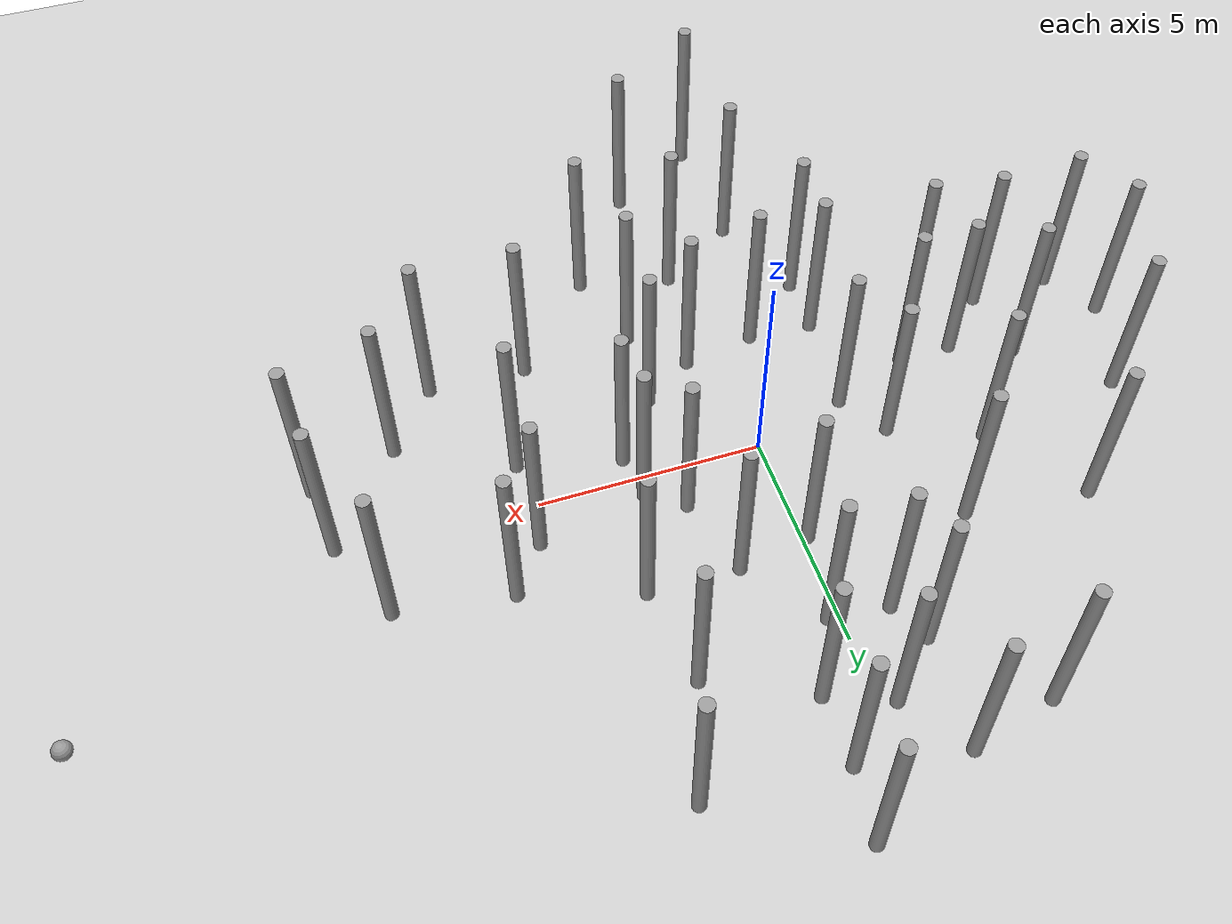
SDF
<sdf version="1.6">
 <world name="default">
  <light name="sun" type="directional">
   <pose>0 0 10 0 -0 0</pose>
   <diffuse>0.8 0.8 0.8 1</diffuse>
   <specular>0.2 0.2 0.2 1</specular>
   <attenuation>
    <range>1000</range>
    <constant>0.9</constant>
    <linear>0.01</linear>
    <quadratic>0.001</quadratic>
   </attenuation>
   <direction>-0.5 0.1 -0.9</direction>
  </light>
  <model name="ground_plane">
   <static>1</static>
   <link name="link">
    <collision name="collision">
     <geometry><plane><normal>0 0 1</normal><size>100 100</size></plane></geometry>
     <surface><friction><ode><mu>100</mu><mu2>50</mu2></ode></friction></surface>
    </collision>
    <visual name="visual">
     <cast_shadows>0</cast_shadows>
     <geometry><plane><normal>0 0 1</normal><size>100 100</size></plane></geometry>
     <material>
      <script><uri>file://media/materials/scripts/gazebo.material</uri><name>Gazebo/Grey</name></script>
     </material>
    </visual>
   </link>
  </model>
  <gravity>0 0 -9.8</gravity>
  <magnetic_field>6e-06 2.3e-05 -4.2e-05</magnetic_field>
  <atmosphere type="adiabatic"/>
  <physics name="default_physics" default="0" type="ode">
   <max_step_size>0.001</max_step_size>
   <real_time_factor>1</real_time_factor>
   <real_time_update_rate>1000</real_time_update_rate>
  </physics>
  <scene><ambient>0.4 0.4 0.4 1</ambient><background>0.7 0.7 0.7 1</background><shadows>1</shadows></scene>
  <spherical_coordinates>
   <surface_model>EARTH_WGS84</surface_model>
   <latitude_deg>0</latitude_deg>
   <longitude_deg>0</longitude_deg>
   <elevation>0</elevation>
   <heading_deg>0</heading_deg>
  </spherical_coordinates>
  <model name="unit_cylinder">
   <link name="link">
    <inertial>
     <mass>1000</mass>
     <inertia><ixx>145.833</ixx><ixy>0</ixy><ixz>0</ixz><iyy>145.833</iyy><iyz>0</iyz><izz>125</izz></inertia>
    </inertial>
    <visual name="visual">
     <geometry><cylinder><radius>0.15</radius><length>4</length></cylinder></geometry>
     <material>
      <script><name>Gazebo/Grey</name><uri>file://media/materials/scripts/gazebo.material</uri></script>
      <shader type="pixel"><normal_map>__default__</normal_map></shader>
      <ambient>0.3 0.3 0.3 1</ambient>
      <diffuse>0.7 0.7 0.7 1</diffuse>
      <specular>0.01 0.01 0.01 1</specular>
      <emissive>0 0 0 1</emissive>
     </material>
    </visual>
    <collision name="collision">
     <geometry><cylinder><radius>0.15</radius><length>4</length></cylinder></geometry>
     <surface>
      <friction>
       <ode><mu>1</mu><mu2>1</mu2><fdir1>0 0 0</fdir1><slip1>0</slip1><slip2>0</slip2></ode>
       <torsional>
        <coefficient>1</coefficient>
        <patch_radius>0</patch_radius>
        <surface_radius>0</surface_radius>
        <use_patch_radius>1</use_patch_radius>
        <ode><slip>0</slip></ode>
       </torsional>
      </friction>
      <bounce><restitution_coefficient>0</restitution_coefficient><threshold>1e+06</threshold></bounce>
      <contact>
       <collide_without_contact>0</collide_without_contact>
       <collide_without_contact_bitmask>1</collide_without_contact_bitmask>
       <collide_bitmask>1</collide_bitmask>
       <ode>
        <soft_cfm>0</soft_cfm>
        <soft_erp>0.2</soft_erp>
        <kp>1e+13</kp>
        <kd>1</kd>
        <max_vel>0.01</max_vel>
        <min_depth>0</min_depth>
       </ode>
       <bullet>
        <split_impulse>1</split_impulse>
        <split_impulse_penetration_threshold>-0.01</split_impulse_penetration_threshold>
        <soft_cfm>0</soft_cfm>
        <soft_erp>0.2</soft_erp>
        <kp>1e+13</kp>
        <kd>1</kd>
       </bullet>
      </contact>
     </surface>
    </collision>
   </link>
   <static>0</static>
   <pose>-2.17183 -0.620816 1.99999 0 -0 0.001339</pose>
  </model>
  <model name="unit_cylinder_clone">
   <link name="link">
    <inertial>
     <mass>1000</mass>
     <inertia><ixx>145.833</ixx><ixy>0</ixy><ixz>0</ixz><iyy>145.833</iyy><iyz>0</iyz><izz>125</izz></inertia>
    </inertial>
    <visual name="visual">
     <geometry><cylinder><radius>0.15</radius><length>4</length></cylinder></geometry>
     <material>
      <script><name>Gazebo/Grey</name><uri>file://media/materials/scripts/gazebo.material</uri></script>
      <shader type="pixel"><normal_map>__default__</normal_map></shader>
      <ambient>0.3 0.3 0.3 1</ambient>
      <diffuse>0.7 0.7 0.7 1</diffuse>
      <specular>0.01 0.01 0.01 1</specular>
      <emissive>0 0 0 1</emissive>
     </material>
    </visual>
    <collision name="collision">
     <geometry><cylinder><radius>0.15</radius><length>4</length></cylinder></geometry>
     <surface>
      <friction>
       <ode><mu>1</mu><mu2>1</mu2><fdir1>0 0 0</fdir1><slip1>0</slip1><slip2>0</slip2></ode>
       <torsional>
        <coefficient>1</coefficient>
        <patch_radius>0</patch_radius>
        <surface_radius>0</surface_radius>
        <use_patch_radius>1</use_patch_radius>
        <ode><slip>0</slip></ode>
       </torsional>
      </friction>
      <bounce><restitution_coefficient>0</restitution_coefficient><threshold>1e+06</threshold></bounce>
      <contact>
       <collide_without_contact>0</collide_without_contact>
       <collide_without_contact_bitmask>1</collide_without_contact_bitmask>
       <collide_bitmask>1</collide_bitmask>
       <ode>
        <soft_cfm>0</soft_cfm>
        <soft_erp>0.2</soft_erp>
        <kp>1e+13</kp>
        <kd>1</kd>
        <max_vel>0.01</max_vel>
        <min_depth>0</min_depth>
       </ode>
       <bullet>
        <split_impulse>1</split_impulse>
        <split_impulse_penetration_threshold>-0.01</split_impulse_penetration_threshold>
        <soft_cfm>0</soft_cfm>
        <soft_erp>0.2</soft_erp>
        <kp>1e+13</kp>
        <kd>1</kd>
       </bullet>
      </contact>
     </surface>
    </collision>
   </link>
   <static>0</static>
   <pose>2.79096 0.434784 2 0 -0 0.001323</pose>
  </model>
  <model name="unit_cylinder_clone_0">
   <link name="link">
    <inertial>
     <mass>1000</mass>
     <inertia><ixx>145.833</ixx><ixy>0</ixy><ixz>0</ixz><iyy>145.833</iyy><iyz>0</iyz><izz>125</izz></inertia>
    </inertial>
    <visual name="visual">
     <geometry><cylinder><radius>0.15</radius><length>4</length></cylinder></geometry>
     <material>
      <script><name>Gazebo/Grey</name><uri>file://media/materials/scripts/gazebo.material</uri></script>
      <shader type="pixel"><normal_map>__default__</normal_map></shader>
      <ambient>0.3 0.3 0.3 1</ambient>
      <diffuse>0.7 0.7 0.7 1</diffuse>
      <specular>0.01 0.01 0.01 1</specular>
      <emissive>0 0 0 1</emissive>
     </material>
    </visual>
    <collision name="collision">
     <geometry><cylinder><radius>0.15</radius><length>4</length></cylinder></geometry>
     <surface>
      <friction>
       <ode><mu>1</mu><mu2>1</mu2><fdir1>0 0 0</fdir1><slip1>0</slip1><slip2>0</slip2></ode>
       <torsional>
        <coefficient>1</coefficient>
        <patch_radius>0</patch_radius>
        <surface_radius>0</surface_radius>
        <use_patch_radius>1</use_patch_radius>
        <ode><slip>0</slip></ode>
       </torsional>
      </friction>
      <bounce><restitution_coefficient>0</restitution_coefficient><threshold>1e+06</threshold></bounce>
      <contact>
       <collide_without_contact>0</collide_without_contact>
       <collide_without_contact_bitmask>1</collide_without_contact_bitmask>
       <collide_bitmask>1</collide_bitmask>
       <ode>
        <soft_cfm>0</soft_cfm>
        <soft_erp>0.2</soft_erp>
        <kp>1e+13</kp>
        <kd>1</kd>
        <max_vel>0.01</max_vel>
        <min_depth>0</min_depth>
       </ode>
       <bullet>
        <split_impulse>1</split_impulse>
        <split_impulse_penetration_threshold>-0.01</split_impulse_penetration_threshold>
        <soft_cfm>0</soft_cfm>
        <soft_erp>0.2</soft_erp>
        <kp>1e+13</kp>
        <kd>1</kd>
       </bullet>
      </contact>
     </surface>
    </collision>
   </link>
   <static>0</static>
   <pose>-0.126051 2.52884 1.99999 0 -0 0.00133</pose>
  </model>
  <model name="unit_cylinder_clone_1">
   <link name="link">
    <inertial>
     <mass>1000</mass>
     <inertia><ixx>145.833</ixx><ixy>0</ixy><ixz>0</ixz><iyy>145.833</iyy><iyz>0</iyz><izz>125</izz></inertia>
    </inertial>
    <visual name="visual">
     <geometry><cylinder><radius>0.15</radius><length>4</length></cylinder></geometry>
     <material>
      <script><name>Gazebo/Grey</name><uri>file://media/materials/scripts/gazebo.material</uri></script>
      <shader type="pixel"><normal_map>__default__</normal_map></shader>
      <ambient>0.3 0.3 0.3 1</ambient>
      <diffuse>0.7 0.7 0.7 1</diffuse>
      <specular>0.01 0.01 0.01 1</specular>
      <emissive>0 0 0 1</emissive>
     </material>
    </visual>
    <collision name="collision">
     <geometry><cylinder><radius>0.15</radius><length>4</length></cylinder></geometry>
     <surface>
      <friction>
       <ode><mu>1</mu><mu2>1</mu2><fdir1>0 0 0</fdir1><slip1>0</slip1><slip2>0</slip2></ode>
       <torsional>
        <coefficient>1</coefficient>
        <patch_radius>0</patch_radius>
        <surface_radius>0</surface_radius>
        <use_patch_radius>1</use_patch_radius>
        <ode><slip>0</slip></ode>
       </torsional>
      </friction>
      <bounce><restitution_coefficient>0</restitution_coefficient><threshold>1e+06</threshold></bounce>
      <contact>
       <collide_without_contact>0</collide_without_contact>
       <collide_without_contact_bitmask>1</collide_without_contact_bitmask>
       <collide_bitmask>1</collide_bitmask>
       <ode>
        <soft_cfm>0</soft_cfm>
        <soft_erp>0.2</soft_erp>
        <kp>1e+13</kp>
        <kd>1</kd>
        <max_vel>0.01</max_vel>
        <min_depth>0</min_depth>
       </ode>
       <bullet>
        <split_impulse>1</split_impulse>
        <split_impulse_penetration_threshold>-0.01</split_impulse_penetration_threshold>
        <soft_cfm>0</soft_cfm>
        <soft_erp>0.2</soft_erp>
        <kp>1e+13</kp>
        <kd>1</kd>
       </bullet>
      </contact>
     </surface>
    </collision>
   </link>
   <static>0</static>
   <pose>1.48874 2.81377 1.99999 0 0 -0.000338</pose>
  </model>
  <model name="unit_cylinder_clone_2">
   <link name="link">
    <inertial>
     <mass>1000</mass>
     <inertia><ixx>145.833</ixx><ixy>0</ixy><ixz>0</ixz><iyy>145.833</iyy><iyz>0</iyz><izz>125</izz></inertia>
    </inertial>
    <visual name="visual">
     <geometry><cylinder><radius>0.15</radius><length>4</length></cylinder></geometry>
     <material>
      <script><name>Gazebo/Grey</name><uri>file://media/materials/scripts/gazebo.material</uri></script>
      <shader type="pixel"><normal_map>__default__</normal_map></shader>
      <ambient>0.3 0.3 0.3 1</ambient>
      <diffuse>0.7 0.7 0.7 1</diffuse>
      <specular>0.01 0.01 0.01 1</specular>
      <emissive>0 0 0 1</emissive>
     </material>
    </visual>
    <collision name="collision">
     <geometry><cylinder><radius>0.15</radius><length>4</length></cylinder></geometry>
     <surface>
      <friction>
       <ode><mu>1</mu><mu2>1</mu2><fdir1>0 0 0</fdir1><slip1>0</slip1><slip2>0</slip2></ode>
       <torsional>
        <coefficient>1</coefficient>
        <patch_radius>0</patch_radius>
        <surface_radius>0</surface_radius>
        <use_patch_radius>1</use_patch_radius>
        <ode><slip>0</slip></ode>
       </torsional>
      </friction>
      <bounce><restitution_coefficient>0</restitution_coefficient><threshold>1e+06</threshold></bounce>
      <contact>
       <collide_without_contact>0</collide_without_contact>
       <collide_without_contact_bitmask>1</collide_without_contact_bitmask>
       <collide_bitmask>1</collide_bitmask>
       <ode>
        <soft_cfm>0</soft_cfm>
        <soft_erp>0.2</soft_erp>
        <kp>1e+13</kp>
        <kd>1</kd>
        <max_vel>0.01</max_vel>
        <min_depth>0</min_depth>
       </ode>
       <bullet>
        <split_impulse>1</split_impulse>
        <split_impulse_penetration_threshold>-0.01</split_impulse_penetration_threshold>
        <soft_cfm>0</soft_cfm>
        <soft_erp>0.2</soft_erp>
        <kp>1e+13</kp>
        <kd>1</kd>
       </bullet>
      </contact>
     </surface>
    </collision>
   </link>
   <static>0</static>
   <pose>-1.07339 4.59004 1.99999 0 -0 0.001251</pose>
  </model>
  <model name="unit_cylinder_clone_3">
   <link name="link">
    <inertial>
     <mass>1000</mass>
     <inertia><ixx>145.833</ixx><ixy>0</ixy><ixz>0</ixz><iyy>145.833</iyy><iyz>0</iyz><izz>125</izz></inertia>
    </inertial>
    <visual name="visual">
     <geometry><cylinder><radius>0.15</radius><length>4</length></cylinder></geometry>
     <material>
      <script><name>Gazebo/Grey</name><uri>file://media/materials/scripts/gazebo.material</uri></script>
      <shader type="pixel"><normal_map>__default__</normal_map></shader>
      <ambient>0.3 0.3 0.3 1</ambient>
      <diffuse>0.7 0.7 0.7 1</diffuse>
      <specular>0.01 0.01 0.01 1</specular>
      <emissive>0 0 0 1</emissive>
     </material>
    </visual>
    <collision name="collision">
     <geometry><cylinder><radius>0.15</radius><length>4</length></cylinder></geometry>
     <surface>
      <friction>
       <ode><mu>1</mu><mu2>1</mu2><fdir1>0 0 0</fdir1><slip1>0</slip1><slip2>0</slip2></ode>
       <torsional>
        <coefficient>1</coefficient>
        <patch_radius>0</patch_radius>
        <surface_radius>0</surface_radius>
        <use_patch_radius>1</use_patch_radius>
        <ode><slip>0</slip></ode>
       </torsional>
      </friction>
      <bounce><restitution_coefficient>0</restitution_coefficient><threshold>1e+06</threshold></bounce>
      <contact>
       <collide_without_contact>0</collide_without_contact>
       <collide_without_contact_bitmask>1</collide_without_contact_bitmask>
       <collide_bitmask>1</collide_bitmask>
       <ode>
        <soft_cfm>0</soft_cfm>
        <soft_erp>0.2</soft_erp>
        <kp>1e+13</kp>
        <kd>1</kd>
        <max_vel>0.01</max_vel>
        <min_depth>0</min_depth>
       </ode>
       <bullet>
        <split_impulse>1</split_impulse>
        <split_impulse_penetration_threshold>-0.01</split_impulse_penetration_threshold>
        <soft_cfm>0</soft_cfm>
        <soft_erp>0.2</soft_erp>
        <kp>1e+13</kp>
        <kd>1</kd>
       </bullet>
      </contact>
     </surface>
    </collision>
   </link>
   <static>0</static>
   <pose>1.00001 6.00007 1.99999 0 -0 0.00126</pose>
  </model>
  <model name="unit_cylinder_clone_4">
   <link name="link">
    <inertial>
     <mass>1000</mass>
     <inertia><ixx>145.833</ixx><ixy>0</ixy><ixz>0</ixz><iyy>145.833</iyy><iyz>0</iyz><izz>125</izz></inertia>
    </inertial>
    <visual name="visual">
     <geometry><cylinder><radius>0.15</radius><length>4</length></cylinder></geometry>
     <material>
      <script><name>Gazebo/Grey</name><uri>file://media/materials/scripts/gazebo.material</uri></script>
      <shader type="pixel"><normal_map>__default__</normal_map></shader>
      <ambient>0.3 0.3 0.3 1</ambient>
      <diffuse>0.7 0.7 0.7 1</diffuse>
      <specular>0.01 0.01 0.01 1</specular>
      <emissive>0 0 0 1</emissive>
     </material>
    </visual>
    <collision name="collision">
     <geometry><cylinder><radius>0.15</radius><length>4</length></cylinder></geometry>
     <surface>
      <friction>
       <ode><mu>1</mu><mu2>1</mu2><fdir1>0 0 0</fdir1><slip1>0</slip1><slip2>0</slip2></ode>
       <torsional>
        <coefficient>1</coefficient>
        <patch_radius>0</patch_radius>
        <surface_radius>0</surface_radius>
        <use_patch_radius>1</use_patch_radius>
        <ode><slip>0</slip></ode>
       </torsional>
      </friction>
      <bounce><restitution_coefficient>0</restitution_coefficient><threshold>1e+06</threshold></bounce>
      <contact>
       <collide_without_contact>0</collide_without_contact>
       <collide_without_contact_bitmask>1</collide_without_contact_bitmask>
       <collide_bitmask>1</collide_bitmask>
       <ode>
        <soft_cfm>0</soft_cfm>
        <soft_erp>0.2</soft_erp>
        <kp>1e+13</kp>
        <kd>1</kd>
        <max_vel>0.01</max_vel>
        <min_depth>0</min_depth>
       </ode>
       <bullet>
        <split_impulse>1</split_impulse>
        <split_impulse_penetration_threshold>-0.01</split_impulse_penetration_threshold>
        <soft_cfm>0</soft_cfm>
        <soft_erp>0.2</soft_erp>
        <kp>1e+13</kp>
        <kd>1</kd>
       </bullet>
      </contact>
     </surface>
    </collision>
   </link>
   <static>0</static>
   <pose>-3.98103 -1.32852 1.99999 0 -0 0.001494</pose>
  </model>
  <model name="unit_cylinder_clone_5">
   <link name="link">
    <inertial>
     <mass>1000</mass>
     <inertia><ixx>145.833</ixx><ixy>0</ixy><ixz>0</ixz><iyy>145.833</iyy><iyz>0</iyz><izz>125</izz></inertia>
    </inertial>
    <visual name="visual">
     <geometry><cylinder><radius>0.15</radius><length>4</length></cylinder></geometry>
     <material>
      <script><name>Gazebo/Grey</name><uri>file://media/materials/scripts/gazebo.material</uri></script>
      <shader type="pixel"><normal_map>__default__</normal_map></shader>
      <ambient>0.3 0.3 0.3 1</ambient>
      <diffuse>0.7 0.7 0.7 1</diffuse>
      <specular>0.01 0.01 0.01 1</specular>
      <emissive>0 0 0 1</emissive>
     </material>
    </visual>
    <collision name="collision">
     <geometry><cylinder><radius>0.15</radius><length>4</length></cylinder></geometry>
     <surface>
      <friction>
       <ode><mu>1</mu><mu2>1</mu2><fdir1>0 0 0</fdir1><slip1>0</slip1><slip2>0</slip2></ode>
       <torsional>
        <coefficient>1</coefficient>
        <patch_radius>0</patch_radius>
        <surface_radius>0</surface_radius>
        <use_patch_radius>1</use_patch_radius>
        <ode><slip>0</slip></ode>
       </torsional>
      </friction>
      <bounce><restitution_coefficient>0</restitution_coefficient><threshold>1e+06</threshold></bounce>
      <contact>
       <collide_without_contact>0</collide_without_contact>
       <collide_without_contact_bitmask>1</collide_without_contact_bitmask>
       <collide_bitmask>1</collide_bitmask>
       <ode>
        <soft_cfm>0</soft_cfm>
        <soft_erp>0.2</soft_erp>
        <kp>1e+13</kp>
        <kd>1</kd>
        <max_vel>0.01</max_vel>
        <min_depth>0</min_depth>
       </ode>
       <bullet>
        <split_impulse>1</split_impulse>
        <split_impulse_penetration_threshold>-0.01</split_impulse_penetration_threshold>
        <soft_cfm>0</soft_cfm>
        <soft_erp>0.2</soft_erp>
        <kp>1e+13</kp>
        <kd>1</kd>
       </bullet>
      </contact>
     </surface>
    </collision>
   </link>
   <static>0</static>
   <pose>-4.8156 1.25333 2 0 -0 0.00141</pose>
  </model>
  <model name="unit_cylinder_clone_6">
   <link name="link">
    <inertial>
     <mass>1000</mass>
     <inertia><ixx>145.833</ixx><ixy>0</ixy><ixz>0</ixz><iyy>145.833</iyy><iyz>0</iyz><izz>125</izz></inertia>
    </inertial>
    <visual name="visual">
     <geometry><cylinder><radius>0.15</radius><length>4</length></cylinder></geometry>
     <material>
      <script><name>Gazebo/Grey</name><uri>file://media/materials/scripts/gazebo.material</uri></script>
      <shader type="pixel"><normal_map>__default__</normal_map></shader>
      <ambient>0.3 0.3 0.3 1</ambient>
      <diffuse>0.7 0.7 0.7 1</diffuse>
      <specular>0.01 0.01 0.01 1</specular>
      <emissive>0 0 0 1</emissive>
     </material>
    </visual>
    <collision name="collision">
     <geometry><cylinder><radius>0.15</radius><length>4</length></cylinder></geometry>
     <surface>
      <friction>
       <ode><mu>1</mu><mu2>1</mu2><fdir1>0 0 0</fdir1><slip1>0</slip1><slip2>0</slip2></ode>
       <torsional>
        <coefficient>1</coefficient>
        <patch_radius>0</patch_radius>
        <surface_radius>0</surface_radius>
        <use_patch_radius>1</use_patch_radius>
        <ode><slip>0</slip></ode>
       </torsional>
      </friction>
      <bounce><restitution_coefficient>0</restitution_coefficient><threshold>1e+06</threshold></bounce>
      <contact>
       <collide_without_contact>0</collide_without_contact>
       <collide_without_contact_bitmask>1</collide_without_contact_bitmask>
       <collide_bitmask>1</collide_bitmask>
       <ode>
        <soft_cfm>0</soft_cfm>
        <soft_erp>0.2</soft_erp>
        <kp>1e+13</kp>
        <kd>1</kd>
        <max_vel>0.01</max_vel>
        <min_depth>0</min_depth>
       </ode>
       <bullet>
        <split_impulse>1</split_impulse>
        <split_impulse_penetration_threshold>-0.01</split_impulse_penetration_threshold>
        <soft_cfm>0</soft_cfm>
        <soft_erp>0.2</soft_erp>
        <kp>1e+13</kp>
        <kd>1</kd>
       </bullet>
      </contact>
     </surface>
    </collision>
   </link>
   <static>0</static>
   <pose>-3.52334 3.00007 1.99999 0 -0 0.001273</pose>
  </model>
  <model name="unit_cylinder_clone_7">
   <link name="link">
    <inertial>
     <mass>1000</mass>
     <inertia><ixx>145.833</ixx><ixy>0</ixy><ixz>0</ixz><iyy>145.833</iyy><iyz>0</iyz><izz>125</izz></inertia>
    </inertial>
    <visual name="visual">
     <geometry><cylinder><radius>0.15</radius><length>4</length></cylinder></geometry>
     <material>
      <script><name>Gazebo/Grey</name><uri>file://media/materials/scripts/gazebo.material</uri></script>
      <shader type="pixel"><normal_map>__default__</normal_map></shader>
      <ambient>0.3 0.3 0.3 1</ambient>
      <diffuse>0.7 0.7 0.7 1</diffuse>
      <specular>0.01 0.01 0.01 1</specular>
      <emissive>0 0 0 1</emissive>
     </material>
    </visual>
    <collision name="collision">
     <geometry><cylinder><radius>0.15</radius><length>4</length></cylinder></geometry>
     <surface>
      <friction>
       <ode><mu>1</mu><mu2>1</mu2><fdir1>0 0 0</fdir1><slip1>0</slip1><slip2>0</slip2></ode>
       <torsional>
        <coefficient>1</coefficient>
        <patch_radius>0</patch_radius>
        <surface_radius>0</surface_radius>
        <use_patch_radius>1</use_patch_radius>
        <ode><slip>0</slip></ode>
       </torsional>
      </friction>
      <bounce><restitution_coefficient>0</restitution_coefficient><threshold>1e+06</threshold></bounce>
      <contact>
       <collide_without_contact>0</collide_without_contact>
       <collide_without_contact_bitmask>1</collide_without_contact_bitmask>
       <collide_bitmask>1</collide_bitmask>
       <ode>
        <soft_cfm>0</soft_cfm>
        <soft_erp>0.2</soft_erp>
        <kp>1e+13</kp>
        <kd>1</kd>
        <max_vel>0.01</max_vel>
        <min_depth>0</min_depth>
       </ode>
       <bullet>
        <split_impulse>1</split_impulse>
        <split_impulse_penetration_threshold>-0.01</split_impulse_penetration_threshold>
        <soft_cfm>0</soft_cfm>
        <soft_erp>0.2</soft_erp>
        <kp>1e+13</kp>
        <kd>1</kd>
       </bullet>
      </contact>
     </surface>
    </collision>
   </link>
   <static>0</static>
   <pose>-2.40002 -2.93198 1.99999 0 -0 0.001374</pose>
  </model>
  <model name="unit_cylinder_clone_8">
   <link name="link">
    <inertial>
     <mass>1000</mass>
     <inertia><ixx>145.833</ixx><ixy>0</ixy><ixz>0</ixz><iyy>145.833</iyy><iyz>0</iyz><izz>125</izz></inertia>
    </inertial>
    <visual name="visual">
     <geometry><cylinder><radius>0.15</radius><length>4</length></cylinder></geometry>
     <material>
      <script><name>Gazebo/Grey</name><uri>file://media/materials/scripts/gazebo.material</uri></script>
      <shader type="pixel"><normal_map>__default__</normal_map></shader>
      <ambient>0.3 0.3 0.3 1</ambient>
      <diffuse>0.7 0.7 0.7 1</diffuse>
      <specular>0.01 0.01 0.01 1</specular>
      <emissive>0 0 0 1</emissive>
     </material>
    </visual>
    <collision name="collision">
     <geometry><cylinder><radius>0.15</radius><length>4</length></cylinder></geometry>
     <surface>
      <friction>
       <ode><mu>1</mu><mu2>1</mu2><fdir1>0 0 0</fdir1><slip1>0</slip1><slip2>0</slip2></ode>
       <torsional>
        <coefficient>1</coefficient>
        <patch_radius>0</patch_radius>
        <surface_radius>0</surface_radius>
        <use_patch_radius>1</use_patch_radius>
        <ode><slip>0</slip></ode>
       </torsional>
      </friction>
      <bounce><restitution_coefficient>0</restitution_coefficient><threshold>1e+06</threshold></bounce>
      <contact>
       <collide_without_contact>0</collide_without_contact>
       <collide_without_contact_bitmask>1</collide_without_contact_bitmask>
       <collide_bitmask>1</collide_bitmask>
       <ode>
        <soft_cfm>0</soft_cfm>
        <soft_erp>0.2</soft_erp>
        <kp>1e+13</kp>
        <kd>1</kd>
        <max_vel>0.01</max_vel>
        <min_depth>0</min_depth>
       </ode>
       <bullet>
        <split_impulse>1</split_impulse>
        <split_impulse_penetration_threshold>-0.01</split_impulse_penetration_threshold>
        <soft_cfm>0</soft_cfm>
        <soft_erp>0.2</soft_erp>
        <kp>1e+13</kp>
        <kd>1</kd>
       </bullet>
      </contact>
     </surface>
    </collision>
   </link>
   <static>0</static>
   <pose>-2.8562 0.444327 1.99999 0 -0 0.001326</pose>
  </model>
  <model name="unit_cylinder_clone_10">
   <link name="link">
    <inertial>
     <mass>1000</mass>
     <inertia><ixx>145.833</ixx><ixy>0</ixy><ixz>0</ixz><iyy>145.833</iyy><iyz>0</iyz><izz>125</izz></inertia>
    </inertial>
    <visual name="visual">
     <geometry><cylinder><radius>0.15</radius><length>4</length></cylinder></geometry>
     <material>
      <script><name>Gazebo/Grey</name><uri>file://media/materials/scripts/gazebo.material</uri></script>
      <shader type="pixel"><normal_map>__default__</normal_map></shader>
      <ambient>0.3 0.3 0.3 1</ambient>
      <diffuse>0.7 0.7 0.7 1</diffuse>
      <specular>0.01 0.01 0.01 1</specular>
      <emissive>0 0 0 1</emissive>
     </material>
    </visual>
    <collision name="collision">
     <geometry><cylinder><radius>0.15</radius><length>4</length></cylinder></geometry>
     <surface>
      <friction>
       <ode><mu>1</mu><mu2>1</mu2><fdir1>0 0 0</fdir1><slip1>0</slip1><slip2>0</slip2></ode>
       <torsional>
        <coefficient>1</coefficient>
        <patch_radius>0</patch_radius>
        <surface_radius>0</surface_radius>
        <use_patch_radius>1</use_patch_radius>
        <ode><slip>0</slip></ode>
       </torsional>
      </friction>
      <bounce><restitution_coefficient>0</restitution_coefficient><threshold>1e+06</threshold></bounce>
      <contact>
       <collide_without_contact>0</collide_without_contact>
       <collide_without_contact_bitmask>1</collide_without_contact_bitmask>
       <collide_bitmask>1</collide_bitmask>
       <ode>
        <soft_cfm>0</soft_cfm>
        <soft_erp>0.2</soft_erp>
        <kp>1e+13</kp>
        <kd>1</kd>
        <max_vel>0.01</max_vel>
        <min_depth>0</min_depth>
       </ode>
       <bullet>
        <split_impulse>1</split_impulse>
        <split_impulse_penetration_threshold>-0.01</split_impulse_penetration_threshold>
        <soft_cfm>0</soft_cfm>
        <soft_erp>0.2</soft_erp>
        <kp>1e+13</kp>
        <kd>1</kd>
       </bullet>
      </contact>
     </surface>
    </collision>
   </link>
   <static>0</static>
   <pose>-6.4237 -2.50135 1.99999 0 -0 0.001436</pose>
  </model>
  <model name="unit_cylinder_clone_11">
   <link name="link">
    <inertial>
     <mass>1000</mass>
     <inertia><ixx>145.833</ixx><ixy>0</ixy><ixz>0</ixz><iyy>145.833</iyy><iyz>0</iyz><izz>125</izz></inertia>
    </inertial>
    <visual name="visual">
     <geometry><cylinder><radius>0.15</radius><length>4</length></cylinder></geometry>
     <material>
      <script><name>Gazebo/Grey</name><uri>file://media/materials/scripts/gazebo.material</uri></script>
      <shader type="pixel"><normal_map>__default__</normal_map></shader>
      <ambient>0.3 0.3 0.3 1</ambient>
      <diffuse>0.7 0.7 0.7 1</diffuse>
      <specular>0.01 0.01 0.01 1</specular>
      <emissive>0 0 0 1</emissive>
     </material>
    </visual>
    <collision name="collision">
     <geometry><cylinder><radius>0.15</radius><length>4</length></cylinder></geometry>
     <surface>
      <friction>
       <ode><mu>1</mu><mu2>1</mu2><fdir1>0 0 0</fdir1><slip1>0</slip1><slip2>0</slip2></ode>
       <torsional>
        <coefficient>1</coefficient>
        <patch_radius>0</patch_radius>
        <surface_radius>0</surface_radius>
        <use_patch_radius>1</use_patch_radius>
        <ode><slip>0</slip></ode>
       </torsional>
      </friction>
      <bounce><restitution_coefficient>0</restitution_coefficient><threshold>1e+06</threshold></bounce>
      <contact>
       <collide_without_contact>0</collide_without_contact>
       <collide_without_contact_bitmask>1</collide_without_contact_bitmask>
       <collide_bitmask>1</collide_bitmask>
       <ode>
        <soft_cfm>0</soft_cfm>
        <soft_erp>0.2</soft_erp>
        <kp>1e+13</kp>
        <kd>1</kd>
        <max_vel>0.01</max_vel>
        <min_depth>0</min_depth>
       </ode>
       <bullet>
        <split_impulse>1</split_impulse>
        <split_impulse_penetration_threshold>-0.01</split_impulse_penetration_threshold>
        <soft_cfm>0</soft_cfm>
        <soft_erp>0.2</soft_erp>
        <kp>1e+13</kp>
        <kd>1</kd>
       </bullet>
      </contact>
     </surface>
    </collision>
   </link>
   <static>0</static>
   <pose>-4.89766 -2.73779 1.99999 0 -0 0.001436</pose>
  </model>
  <model name="unit_cylinder_clone_13">
   <link name="link">
    <inertial>
     <mass>1000</mass>
     <inertia><ixx>145.833</ixx><ixy>0</ixy><ixz>0</ixz><iyy>145.833</iyy><iyz>0</iyz><izz>125</izz></inertia>
    </inertial>
    <visual name="visual">
     <geometry><cylinder><radius>0.15</radius><length>4</length></cylinder></geometry>
     <material>
      <script><name>Gazebo/Grey</name><uri>file://media/materials/scripts/gazebo.material</uri></script>
      <shader type="pixel"><normal_map>__default__</normal_map></shader>
      <ambient>0.3 0.3 0.3 1</ambient>
      <diffuse>0.7 0.7 0.7 1</diffuse>
      <specular>0.01 0.01 0.01 1</specular>
      <emissive>0 0 0 1</emissive>
     </material>
    </visual>
    <collision name="collision">
     <geometry><cylinder><radius>0.15</radius><length>4</length></cylinder></geometry>
     <surface>
      <friction>
       <ode><mu>1</mu><mu2>1</mu2><fdir1>0 0 0</fdir1><slip1>0</slip1><slip2>0</slip2></ode>
       <torsional>
        <coefficient>1</coefficient>
        <patch_radius>0</patch_radius>
        <surface_radius>0</surface_radius>
        <use_patch_radius>1</use_patch_radius>
        <ode><slip>0</slip></ode>
       </torsional>
      </friction>
      <bounce><restitution_coefficient>0</restitution_coefficient><threshold>1e+06</threshold></bounce>
      <contact>
       <collide_without_contact>0</collide_without_contact>
       <collide_without_contact_bitmask>1</collide_without_contact_bitmask>
       <collide_bitmask>1</collide_bitmask>
       <ode>
        <soft_cfm>0</soft_cfm>
        <soft_erp>0.2</soft_erp>
        <kp>1e+13</kp>
        <kd>1</kd>
        <max_vel>0.01</max_vel>
        <min_depth>0</min_depth>
       </ode>
       <bullet>
        <split_impulse>1</split_impulse>
        <split_impulse_penetration_threshold>-0.01</split_impulse_penetration_threshold>
        <soft_cfm>0</soft_cfm>
        <soft_erp>0.2</soft_erp>
        <kp>1e+13</kp>
        <kd>1</kd>
       </bullet>
      </contact>
     </surface>
    </collision>
   </link>
   <static>0</static>
   <pose>-5.21834 -1.32988 2 0 -0 0.001384</pose>
  </model>
  <model name="unit_cylinder_clone_14">
   <link name="link">
    <inertial>
     <mass>1000</mass>
     <inertia><ixx>145.833</ixx><ixy>0</ixy><ixz>0</ixz><iyy>145.833</iyy><iyz>0</iyz><izz>125</izz></inertia>
    </inertial>
    <visual name="visual">
     <geometry><cylinder><radius>0.15</radius><length>4</length></cylinder></geometry>
     <material>
      <script><name>Gazebo/Grey</name><uri>file://media/materials/scripts/gazebo.material</uri></script>
      <shader type="pixel"><normal_map>__default__</normal_map></shader>
      <ambient>0.3 0.3 0.3 1</ambient>
      <diffuse>0.7 0.7 0.7 1</diffuse>
      <specular>0.01 0.01 0.01 1</specular>
      <emissive>0 0 0 1</emissive>
     </material>
    </visual>
    <collision name="collision">
     <geometry><cylinder><radius>0.15</radius><length>4</length></cylinder></geometry>
     <surface>
      <friction>
       <ode><mu>1</mu><mu2>1</mu2><fdir1>0 0 0</fdir1><slip1>0</slip1><slip2>0</slip2></ode>
       <torsional>
        <coefficient>1</coefficient>
        <patch_radius>0</patch_radius>
        <surface_radius>0</surface_radius>
        <use_patch_radius>1</use_patch_radius>
        <ode><slip>0</slip></ode>
       </torsional>
      </friction>
      <bounce><restitution_coefficient>0</restitution_coefficient><threshold>1e+06</threshold></bounce>
      <contact>
       <collide_without_contact>0</collide_without_contact>
       <collide_without_contact_bitmask>1</collide_without_contact_bitmask>
       <collide_bitmask>1</collide_bitmask>
       <ode>
        <soft_cfm>0</soft_cfm>
        <soft_erp>0.2</soft_erp>
        <kp>1e+13</kp>
        <kd>1</kd>
        <max_vel>0.01</max_vel>
        <min_depth>0</min_depth>
       </ode>
       <bullet>
        <split_impulse>1</split_impulse>
        <split_impulse_penetration_threshold>-0.01</split_impulse_penetration_threshold>
        <soft_cfm>0</soft_cfm>
        <soft_erp>0.2</soft_erp>
        <kp>1e+13</kp>
        <kd>1</kd>
       </bullet>
      </contact>
     </surface>
    </collision>
   </link>
   <static>0</static>
   <pose>-6.57296 -0.768324 1.99999 0 -0 0.001141</pose>
  </model>
  <model name="unit_cylinder_clone_15">
   <link name="link">
    <inertial>
     <mass>1000</mass>
     <inertia><ixx>145.833</ixx><ixy>0</ixy><ixz>0</ixz><iyy>145.833</iyy><iyz>0</iyz><izz>125</izz></inertia>
    </inertial>
    <visual name="visual">
     <geometry><cylinder><radius>0.15</radius><length>4</length></cylinder></geometry>
     <material>
      <script><name>Gazebo/Grey</name><uri>file://media/materials/scripts/gazebo.material</uri></script>
      <shader type="pixel"><normal_map>__default__</normal_map></shader>
      <ambient>0.3 0.3 0.3 1</ambient>
      <diffuse>0.7 0.7 0.7 1</diffuse>
      <specular>0.01 0.01 0.01 1</specular>
      <emissive>0 0 0 1</emissive>
     </material>
    </visual>
    <collision name="collision">
     <geometry><cylinder><radius>0.15</radius><length>4</length></cylinder></geometry>
     <surface>
      <friction>
       <ode><mu>1</mu><mu2>1</mu2><fdir1>0 0 0</fdir1><slip1>0</slip1><slip2>0</slip2></ode>
       <torsional>
        <coefficient>1</coefficient>
        <patch_radius>0</patch_radius>
        <surface_radius>0</surface_radius>
        <use_patch_radius>1</use_patch_radius>
        <ode><slip>0</slip></ode>
       </torsional>
      </friction>
      <bounce><restitution_coefficient>0</restitution_coefficient><threshold>1e+06</threshold></bounce>
      <contact>
       <collide_without_contact>0</collide_without_contact>
       <collide_without_contact_bitmask>1</collide_without_contact_bitmask>
       <collide_bitmask>1</collide_bitmask>
       <ode>
        <soft_cfm>0</soft_cfm>
        <soft_erp>0.2</soft_erp>
        <kp>1e+13</kp>
        <kd>1</kd>
        <max_vel>0.01</max_vel>
        <min_depth>0</min_depth>
       </ode>
       <bullet>
        <split_impulse>1</split_impulse>
        <split_impulse_penetration_threshold>-0.01</split_impulse_penetration_threshold>
        <soft_cfm>0</soft_cfm>
        <soft_erp>0.2</soft_erp>
        <kp>1e+13</kp>
        <kd>1</kd>
       </bullet>
      </contact>
     </surface>
    </collision>
   </link>
   <static>0</static>
   <pose>-8.32879 -2.56422 2 0 -0 0.001268</pose>
  </model>
  <model name="unit_cylinder_clone_16">
   <link name="link">
    <inertial>
     <mass>1000</mass>
     <inertia><ixx>145.833</ixx><ixy>0</ixy><ixz>0</ixz><iyy>145.833</iyy><iyz>0</iyz><izz>125</izz></inertia>
    </inertial>
    <visual name="visual">
     <geometry><cylinder><radius>0.15</radius><length>4</length></cylinder></geometry>
     <material>
      <script><name>Gazebo/Grey</name><uri>file://media/materials/scripts/gazebo.material</uri></script>
      <shader type="pixel"><normal_map>__default__</normal_map></shader>
      <ambient>0.3 0.3 0.3 1</ambient>
      <diffuse>0.7 0.7 0.7 1</diffuse>
      <specular>0.01 0.01 0.01 1</specular>
      <emissive>0 0 0 1</emissive>
     </material>
    </visual>
    <collision name="collision">
     <geometry><cylinder><radius>0.15</radius><length>4</length></cylinder></geometry>
     <surface>
      <friction>
       <ode><mu>1</mu><mu2>1</mu2><fdir1>0 0 0</fdir1><slip1>0</slip1><slip2>0</slip2></ode>
       <torsional>
        <coefficient>1</coefficient>
        <patch_radius>0</patch_radius>
        <surface_radius>0</surface_radius>
        <use_patch_radius>1</use_patch_radius>
        <ode><slip>0</slip></ode>
       </torsional>
      </friction>
      <bounce><restitution_coefficient>0</restitution_coefficient><threshold>1e+06</threshold></bounce>
      <contact>
       <collide_without_contact>0</collide_without_contact>
       <collide_without_contact_bitmask>1</collide_without_contact_bitmask>
       <collide_bitmask>1</collide_bitmask>
       <ode>
        <soft_cfm>0</soft_cfm>
        <soft_erp>0.2</soft_erp>
        <kp>1e+13</kp>
        <kd>1</kd>
        <max_vel>0.01</max_vel>
        <min_depth>0</min_depth>
       </ode>
       <bullet>
        <split_impulse>1</split_impulse>
        <split_impulse_penetration_threshold>-0.01</split_impulse_penetration_threshold>
        <soft_cfm>0</soft_cfm>
        <soft_erp>0.2</soft_erp>
        <kp>1e+13</kp>
        <kd>1</kd>
       </bullet>
      </contact>
     </surface>
    </collision>
   </link>
   <static>0</static>
   <pose>-9.06637 -1.36031 2 0 -0 0.001316</pose>
  </model>
  <model name="unit_cylinder_clone_17">
   <link name="link">
    <inertial>
     <mass>1000</mass>
     <inertia><ixx>145.833</ixx><ixy>0</ixy><ixz>0</ixz><iyy>145.833</iyy><iyz>0</iyz><izz>125</izz></inertia>
    </inertial>
    <visual name="visual">
     <geometry><cylinder><radius>0.15</radius><length>4</length></cylinder></geometry>
     <material>
      <script><name>Gazebo/Grey</name><uri>file://media/materials/scripts/gazebo.material</uri></script>
      <shader type="pixel"><normal_map>__default__</normal_map></shader>
      <ambient>0.3 0.3 0.3 1</ambient>
      <diffuse>0.7 0.7 0.7 1</diffuse>
      <specular>0.01 0.01 0.01 1</specular>
      <emissive>0 0 0 1</emissive>
     </material>
    </visual>
    <collision name="collision">
     <geometry><cylinder><radius>0.15</radius><length>4</length></cylinder></geometry>
     <surface>
      <friction>
       <ode><mu>1</mu><mu2>1</mu2><fdir1>0 0 0</fdir1><slip1>0</slip1><slip2>0</slip2></ode>
       <torsional>
        <coefficient>1</coefficient>
        <patch_radius>0</patch_radius>
        <surface_radius>0</surface_radius>
        <use_patch_radius>1</use_patch_radius>
        <ode><slip>0</slip></ode>
       </torsional>
      </friction>
      <bounce><restitution_coefficient>0</restitution_coefficient><threshold>1e+06</threshold></bounce>
      <contact>
       <collide_without_contact>0</collide_without_contact>
       <collide_without_contact_bitmask>1</collide_without_contact_bitmask>
       <collide_bitmask>1</collide_bitmask>
       <ode>
        <soft_cfm>0</soft_cfm>
        <soft_erp>0.2</soft_erp>
        <kp>1e+13</kp>
        <kd>1</kd>
        <max_vel>0.01</max_vel>
        <min_depth>0</min_depth>
       </ode>
       <bullet>
        <split_impulse>1</split_impulse>
        <split_impulse_penetration_threshold>-0.01</split_impulse_penetration_threshold>
        <soft_cfm>0</soft_cfm>
        <soft_erp>0.2</soft_erp>
        <kp>1e+13</kp>
        <kd>1</kd>
       </bullet>
      </contact>
     </surface>
    </collision>
   </link>
   <static>0</static>
   <pose>-8.26984 0.791577 1.99999 0 -0 0.001328</pose>
  </model>
  <model name="unit_cylinder_clone_18">
   <link name="link">
    <inertial>
     <mass>1000</mass>
     <inertia><ixx>145.833</ixx><ixy>0</ixy><ixz>0</ixz><iyy>145.833</iyy><iyz>0</iyz><izz>125</izz></inertia>
    </inertial>
    <visual name="visual">
     <geometry><cylinder><radius>0.15</radius><length>4</length></cylinder></geometry>
     <material>
      <script><name>Gazebo/Grey</name><uri>file://media/materials/scripts/gazebo.material</uri></script>
      <shader type="pixel"><normal_map>__default__</normal_map></shader>
      <ambient>0.3 0.3 0.3 1</ambient>
      <diffuse>0.7 0.7 0.7 1</diffuse>
      <specular>0.01 0.01 0.01 1</specular>
      <emissive>0 0 0 1</emissive>
     </material>
    </visual>
    <collision name="collision">
     <geometry><cylinder><radius>0.15</radius><length>4</length></cylinder></geometry>
     <surface>
      <friction>
       <ode><mu>1</mu><mu2>1</mu2><fdir1>0 0 0</fdir1><slip1>0</slip1><slip2>0</slip2></ode>
       <torsional>
        <coefficient>1</coefficient>
        <patch_radius>0</patch_radius>
        <surface_radius>0</surface_radius>
        <use_patch_radius>1</use_patch_radius>
        <ode><slip>0</slip></ode>
       </torsional>
      </friction>
      <bounce><restitution_coefficient>0</restitution_coefficient><threshold>1e+06</threshold></bounce>
      <contact>
       <collide_without_contact>0</collide_without_contact>
       <collide_without_contact_bitmask>1</collide_without_contact_bitmask>
       <collide_bitmask>1</collide_bitmask>
       <ode>
        <soft_cfm>0</soft_cfm>
        <soft_erp>0.2</soft_erp>
        <kp>1e+13</kp>
        <kd>1</kd>
        <max_vel>0.01</max_vel>
        <min_depth>0</min_depth>
       </ode>
       <bullet>
        <split_impulse>1</split_impulse>
        <split_impulse_penetration_threshold>-0.01</split_impulse_penetration_threshold>
        <soft_cfm>0</soft_cfm>
        <soft_erp>0.2</soft_erp>
        <kp>1e+13</kp>
        <kd>1</kd>
       </bullet>
      </contact>
     </surface>
    </collision>
   </link>
   <static>0</static>
   <pose>1.18443 9.01135 2 0 -0 0.00132</pose>
  </model>
  <model name="unit_cylinder_clone_19">
   <link name="link">
    <inertial>
     <mass>1000</mass>
     <inertia><ixx>145.833</ixx><ixy>0</ixy><ixz>0</ixz><iyy>145.833</iyy><iyz>0</iyz><izz>125</izz></inertia>
    </inertial>
    <visual name="visual">
     <geometry><cylinder><radius>0.15</radius><length>4</length></cylinder></geometry>
     <material>
      <script><name>Gazebo/Grey</name><uri>file://media/materials/scripts/gazebo.material</uri></script>
      <shader type="pixel"><normal_map>__default__</normal_map></shader>
      <ambient>0.3 0.3 0.3 1</ambient>
      <diffuse>0.7 0.7 0.7 1</diffuse>
      <specular>0.01 0.01 0.01 1</specular>
      <emissive>0 0 0 1</emissive>
     </material>
    </visual>
    <collision name="collision">
     <geometry><cylinder><radius>0.15</radius><length>4</length></cylinder></geometry>
     <surface>
      <friction>
       <ode><mu>1</mu><mu2>1</mu2><fdir1>0 0 0</fdir1><slip1>0</slip1><slip2>0</slip2></ode>
       <torsional>
        <coefficient>1</coefficient>
        <patch_radius>0</patch_radius>
        <surface_radius>0</surface_radius>
        <use_patch_radius>1</use_patch_radius>
        <ode><slip>0</slip></ode>
       </torsional>
      </friction>
      <bounce><restitution_coefficient>0</restitution_coefficient><threshold>1e+06</threshold></bounce>
      <contact>
       <collide_without_contact>0</collide_without_contact>
       <collide_without_contact_bitmask>1</collide_without_contact_bitmask>
       <collide_bitmask>1</collide_bitmask>
       <ode>
        <soft_cfm>0</soft_cfm>
        <soft_erp>0.2</soft_erp>
        <kp>1e+13</kp>
        <kd>1</kd>
        <max_vel>0.01</max_vel>
        <min_depth>0</min_depth>
       </ode>
       <bullet>
        <split_impulse>1</split_impulse>
        <split_impulse_penetration_threshold>-0.01</split_impulse_penetration_threshold>
        <soft_cfm>0</soft_cfm>
        <soft_erp>0.2</soft_erp>
        <kp>1e+13</kp>
        <kd>1</kd>
       </bullet>
      </contact>
     </surface>
    </collision>
   </link>
   <static>0</static>
   <pose>-3.20769 7.43034 1.99999 0 -0 0.000896</pose>
  </model>
  <model name="unit_cylinder_clone_20">
   <link name="link">
    <inertial>
     <mass>1000</mass>
     <inertia><ixx>145.833</ixx><ixy>0</ixy><ixz>0</ixz><iyy>145.833</iyy><iyz>0</iyz><izz>125</izz></inertia>
    </inertial>
    <visual name="visual">
     <geometry><cylinder><radius>0.15</radius><length>4</length></cylinder></geometry>
     <material>
      <script><name>Gazebo/Grey</name><uri>file://media/materials/scripts/gazebo.material</uri></script>
      <shader type="pixel"><normal_map>__default__</normal_map></shader>
      <ambient>0.3 0.3 0.3 1</ambient>
      <diffuse>0.7 0.7 0.7 1</diffuse>
      <specular>0.01 0.01 0.01 1</specular>
      <emissive>0 0 0 1</emissive>
     </material>
    </visual>
    <collision name="collision">
     <geometry><cylinder><radius>0.15</radius><length>4</length></cylinder></geometry>
     <surface>
      <friction>
       <ode><mu>1</mu><mu2>1</mu2><fdir1>0 0 0</fdir1><slip1>0</slip1><slip2>0</slip2></ode>
       <torsional>
        <coefficient>1</coefficient>
        <patch_radius>0</patch_radius>
        <surface_radius>0</surface_radius>
        <use_patch_radius>1</use_patch_radius>
        <ode><slip>0</slip></ode>
       </torsional>
      </friction>
      <bounce><restitution_coefficient>0</restitution_coefficient><threshold>1e+06</threshold></bounce>
      <contact>
       <collide_without_contact>0</collide_without_contact>
       <collide_without_contact_bitmask>1</collide_without_contact_bitmask>
       <collide_bitmask>1</collide_bitmask>
       <ode>
        <soft_cfm>0</soft_cfm>
        <soft_erp>0.2</soft_erp>
        <kp>1e+13</kp>
        <kd>1</kd>
        <max_vel>0.01</max_vel>
        <min_depth>0</min_depth>
       </ode>
       <bullet>
        <split_impulse>1</split_impulse>
        <split_impulse_penetration_threshold>-0.01</split_impulse_penetration_threshold>
        <soft_cfm>0</soft_cfm>
        <soft_erp>0.2</soft_erp>
        <kp>1e+13</kp>
        <kd>1</kd>
       </bullet>
      </contact>
     </surface>
    </collision>
   </link>
   <static>0</static>
   <pose>3.9803 7.3232 1.99999 0 -0 0.001389</pose>
  </model>
  <model name="unit_cylinder_clone_21">
   <link name="link">
    <inertial>
     <mass>1000</mass>
     <inertia><ixx>145.833</ixx><ixy>0</ixy><ixz>0</ixz><iyy>145.833</iyy><iyz>0</iyz><izz>125</izz></inertia>
    </inertial>
    <visual name="visual">
     <geometry><cylinder><radius>0.15</radius><length>4</length></cylinder></geometry>
     <material>
      <script><name>Gazebo/Grey</name><uri>file://media/materials/scripts/gazebo.material</uri></script>
      <shader type="pixel"><normal_map>__default__</normal_map></shader>
      <ambient>0.3 0.3 0.3 1</ambient>
      <diffuse>0.7 0.7 0.7 1</diffuse>
      <specular>0.01 0.01 0.01 1</specular>
      <emissive>0 0 0 1</emissive>
     </material>
    </visual>
    <collision name="collision">
     <geometry><cylinder><radius>0.15</radius><length>4</length></cylinder></geometry>
     <surface>
      <friction>
       <ode><mu>1</mu><mu2>1</mu2><fdir1>0 0 0</fdir1><slip1>0</slip1><slip2>0</slip2></ode>
       <torsional>
        <coefficient>1</coefficient>
        <patch_radius>0</patch_radius>
        <surface_radius>0</surface_radius>
        <use_patch_radius>1</use_patch_radius>
        <ode><slip>0</slip></ode>
       </torsional>
      </friction>
      <bounce><restitution_coefficient>0</restitution_coefficient><threshold>1e+06</threshold></bounce>
      <contact>
       <collide_without_contact>0</collide_without_contact>
       <collide_without_contact_bitmask>1</collide_without_contact_bitmask>
       <collide_bitmask>1</collide_bitmask>
       <ode>
        <soft_cfm>0</soft_cfm>
        <soft_erp>0.2</soft_erp>
        <kp>1e+13</kp>
        <kd>1</kd>
        <max_vel>0.01</max_vel>
        <min_depth>0</min_depth>
       </ode>
       <bullet>
        <split_impulse>1</split_impulse>
        <split_impulse_penetration_threshold>-0.01</split_impulse_penetration_threshold>
        <soft_cfm>0</soft_cfm>
        <soft_erp>0.2</soft_erp>
        <kp>1e+13</kp>
        <kd>1</kd>
       </bullet>
      </contact>
     </surface>
    </collision>
   </link>
   <static>0</static>
   <pose>-1.30192 7.90799 1.99999 0 0 -0.000854</pose>
  </model>
  <model name="unit_cylinder_clone_22">
   <link name="link">
    <inertial>
     <mass>1000</mass>
     <inertia><ixx>145.833</ixx><ixy>0</ixy><ixz>0</ixz><iyy>145.833</iyy><iyz>0</iyz><izz>125</izz></inertia>
    </inertial>
    <visual name="visual">
     <geometry><cylinder><radius>0.15</radius><length>4</length></cylinder></geometry>
     <material>
      <script><name>Gazebo/Grey</name><uri>file://media/materials/scripts/gazebo.material</uri></script>
      <shader type="pixel"><normal_map>__default__</normal_map></shader>
      <ambient>0.3 0.3 0.3 1</ambient>
      <diffuse>0.7 0.7 0.7 1</diffuse>
      <specular>0.01 0.01 0.01 1</specular>
      <emissive>0 0 0 1</emissive>
     </material>
    </visual>
    <collision name="collision">
     <geometry><cylinder><radius>0.15</radius><length>4</length></cylinder></geometry>
     <surface>
      <friction>
       <ode><mu>1</mu><mu2>1</mu2><fdir1>0 0 0</fdir1><slip1>0</slip1><slip2>0</slip2></ode>
       <torsional>
        <coefficient>1</coefficient>
        <patch_radius>0</patch_radius>
        <surface_radius>0</surface_radius>
        <use_patch_radius>1</use_patch_radius>
        <ode><slip>0</slip></ode>
       </torsional>
      </friction>
      <bounce><restitution_coefficient>0</restitution_coefficient><threshold>1e+06</threshold></bounce>
      <contact>
       <collide_without_contact>0</collide_without_contact>
       <collide_without_contact_bitmask>1</collide_without_contact_bitmask>
       <collide_bitmask>1</collide_bitmask>
       <ode>
        <soft_cfm>0</soft_cfm>
        <soft_erp>0.2</soft_erp>
        <kp>1e+13</kp>
        <kd>1</kd>
        <max_vel>0.01</max_vel>
        <min_depth>0</min_depth>
       </ode>
       <bullet>
        <split_impulse>1</split_impulse>
        <split_impulse_penetration_threshold>-0.01</split_impulse_penetration_threshold>
        <soft_cfm>0</soft_cfm>
        <soft_erp>0.2</soft_erp>
        <kp>1e+13</kp>
        <kd>1</kd>
       </bullet>
      </contact>
     </surface>
    </collision>
   </link>
   <static>0</static>
   <pose>0.989173 7.51328 2 0 -0 0.001145</pose>
  </model>
  <model name="unit_cylinder_clone_23">
   <link name="link">
    <inertial>
     <mass>1000</mass>
     <inertia><ixx>145.833</ixx><ixy>0</ixy><ixz>0</ixz><iyy>145.833</iyy><iyz>0</iyz><izz>125</izz></inertia>
    </inertial>
    <visual name="visual">
     <geometry><cylinder><radius>0.15</radius><length>4</length></cylinder></geometry>
     <material>
      <script><name>Gazebo/Grey</name><uri>file://media/materials/scripts/gazebo.material</uri></script>
      <shader type="pixel"><normal_map>__default__</normal_map></shader>
      <ambient>0.3 0.3 0.3 1</ambient>
      <diffuse>0.7 0.7 0.7 1</diffuse>
      <specular>0.01 0.01 0.01 1</specular>
      <emissive>0 0 0 1</emissive>
     </material>
    </visual>
    <collision name="collision">
     <geometry><cylinder><radius>0.15</radius><length>4</length></cylinder></geometry>
     <surface>
      <friction>
       <ode><mu>1</mu><mu2>1</mu2><fdir1>0 0 0</fdir1><slip1>0</slip1><slip2>0</slip2></ode>
       <torsional>
        <coefficient>1</coefficient>
        <patch_radius>0</patch_radius>
        <surface_radius>0</surface_radius>
        <use_patch_radius>1</use_patch_radius>
        <ode><slip>0</slip></ode>
       </torsional>
      </friction>
      <bounce><restitution_coefficient>0</restitution_coefficient><threshold>1e+06</threshold></bounce>
      <contact>
       <collide_without_contact>0</collide_without_contact>
       <collide_without_contact_bitmask>1</collide_without_contact_bitmask>
       <collide_bitmask>1</collide_bitmask>
       <ode>
        <soft_cfm>0</soft_cfm>
        <soft_erp>0.2</soft_erp>
        <kp>1e+13</kp>
        <kd>1</kd>
        <max_vel>0.01</max_vel>
        <min_depth>0</min_depth>
       </ode>
       <bullet>
        <split_impulse>1</split_impulse>
        <split_impulse_penetration_threshold>-0.01</split_impulse_penetration_threshold>
        <soft_cfm>0</soft_cfm>
        <soft_erp>0.2</soft_erp>
        <kp>1e+13</kp>
        <kd>1</kd>
       </bullet>
      </contact>
     </surface>
    </collision>
   </link>
   <static>0</static>
   <pose>0.228998 4.44918 1.99999 0 -0 0.000973</pose>
  </model>
  <model name="unit_cylinder_clone_24">
   <link name="link">
    <inertial>
     <mass>1000</mass>
     <inertia><ixx>145.833</ixx><ixy>0</ixy><ixz>0</ixz><iyy>145.833</iyy><iyz>0</iyz><izz>125</izz></inertia>
    </inertial>
    <visual name="visual">
     <geometry><cylinder><radius>0.15</radius><length>4</length></cylinder></geometry>
     <material>
      <script><name>Gazebo/Grey</name><uri>file://media/materials/scripts/gazebo.material</uri></script>
      <shader type="pixel"><normal_map>__default__</normal_map></shader>
      <ambient>0.3 0.3 0.3 1</ambient>
      <diffuse>0.7 0.7 0.7 1</diffuse>
      <specular>0.01 0.01 0.01 1</specular>
      <emissive>0 0 0 1</emissive>
     </material>
    </visual>
    <collision name="collision">
     <geometry><cylinder><radius>0.15</radius><length>4</length></cylinder></geometry>
     <surface>
      <friction>
       <ode><mu>1</mu><mu2>1</mu2><fdir1>0 0 0</fdir1><slip1>0</slip1><slip2>0</slip2></ode>
       <torsional>
        <coefficient>1</coefficient>
        <patch_radius>0</patch_radius>
        <surface_radius>0</surface_radius>
        <use_patch_radius>1</use_patch_radius>
        <ode><slip>0</slip></ode>
       </torsional>
      </friction>
      <bounce><restitution_coefficient>0</restitution_coefficient><threshold>1e+06</threshold></bounce>
      <contact>
       <collide_without_contact>0</collide_without_contact>
       <collide_without_contact_bitmask>1</collide_without_contact_bitmask>
       <collide_bitmask>1</collide_bitmask>
       <ode>
        <soft_cfm>0</soft_cfm>
        <soft_erp>0.2</soft_erp>
        <kp>1e+13</kp>
        <kd>1</kd>
        <max_vel>0.01</max_vel>
        <min_depth>0</min_depth>
       </ode>
       <bullet>
        <split_impulse>1</split_impulse>
        <split_impulse_penetration_threshold>-0.01</split_impulse_penetration_threshold>
        <soft_cfm>0</soft_cfm>
        <soft_erp>0.2</soft_erp>
        <kp>1e+13</kp>
        <kd>1</kd>
       </bullet>
      </contact>
     </surface>
    </collision>
   </link>
   <static>0</static>
   <pose>3.1593 4.96127 2 0 -0 0.000918</pose>
  </model>
  <model name="unit_cylinder_clone_25">
   <link name="link">
    <inertial>
     <mass>1000</mass>
     <inertia><ixx>145.833</ixx><ixy>0</ixy><ixz>0</ixz><iyy>145.833</iyy><iyz>0</iyz><izz>125</izz></inertia>
    </inertial>
    <visual name="visual">
     <geometry><cylinder><radius>0.15</radius><length>4</length></cylinder></geometry>
     <material>
      <script><name>Gazebo/Grey</name><uri>file://media/materials/scripts/gazebo.material</uri></script>
      <shader type="pixel"><normal_map>__default__</normal_map></shader>
      <ambient>0.3 0.3 0.3 1</ambient>
      <diffuse>0.7 0.7 0.7 1</diffuse>
      <specular>0.01 0.01 0.01 1</specular>
      <emissive>0 0 0 1</emissive>
     </material>
    </visual>
    <collision name="collision">
     <geometry><cylinder><radius>0.15</radius><length>4</length></cylinder></geometry>
     <surface>
      <friction>
       <ode><mu>1</mu><mu2>1</mu2><fdir1>0 0 0</fdir1><slip1>0</slip1><slip2>0</slip2></ode>
       <torsional>
        <coefficient>1</coefficient>
        <patch_radius>0</patch_radius>
        <surface_radius>0</surface_radius>
        <use_patch_radius>1</use_patch_radius>
        <ode><slip>0</slip></ode>
       </torsional>
      </friction>
      <bounce><restitution_coefficient>0</restitution_coefficient><threshold>1e+06</threshold></bounce>
      <contact>
       <collide_without_contact>0</collide_without_contact>
       <collide_without_contact_bitmask>1</collide_without_contact_bitmask>
       <collide_bitmask>1</collide_bitmask>
       <ode>
        <soft_cfm>0</soft_cfm>
        <soft_erp>0.2</soft_erp>
        <kp>1e+13</kp>
        <kd>1</kd>
        <max_vel>0.01</max_vel>
        <min_depth>0</min_depth>
       </ode>
       <bullet>
        <split_impulse>1</split_impulse>
        <split_impulse_penetration_threshold>-0.01</split_impulse_penetration_threshold>
        <soft_cfm>0</soft_cfm>
        <soft_erp>0.2</soft_erp>
        <kp>1e+13</kp>
        <kd>1</kd>
       </bullet>
      </contact>
     </surface>
    </collision>
   </link>
   <static>0</static>
   <pose>-1.48648 5.46286 2 0 -0 0.001333</pose>
  </model>
  <model name="unit_cylinder_clone_26">
   <link name="link">
    <inertial>
     <mass>1000</mass>
     <inertia><ixx>145.833</ixx><ixy>0</ixy><ixz>0</ixz><iyy>145.833</iyy><iyz>0</iyz><izz>125</izz></inertia>
    </inertial>
    <visual name="visual">
     <geometry><cylinder><radius>0.15</radius><length>4</length></cylinder></geometry>
     <material>
      <script><name>Gazebo/Grey</name><uri>file://media/materials/scripts/gazebo.material</uri></script>
      <shader type="pixel"><normal_map>__default__</normal_map></shader>
      <ambient>0.3 0.3 0.3 1</ambient>
      <diffuse>0.7 0.7 0.7 1</diffuse>
      <specular>0.01 0.01 0.01 1</specular>
      <emissive>0 0 0 1</emissive>
     </material>
    </visual>
    <collision name="collision">
     <geometry><cylinder><radius>0.15</radius><length>4</length></cylinder></geometry>
     <surface>
      <friction>
       <ode><mu>1</mu><mu2>1</mu2><fdir1>0 0 0</fdir1><slip1>0</slip1><slip2>0</slip2></ode>
       <torsional>
        <coefficient>1</coefficient>
        <patch_radius>0</patch_radius>
        <surface_radius>0</surface_radius>
        <use_patch_radius>1</use_patch_radius>
        <ode><slip>0</slip></ode>
       </torsional>
      </friction>
      <bounce><restitution_coefficient>0</restitution_coefficient><threshold>1e+06</threshold></bounce>
      <contact>
       <collide_without_contact>0</collide_without_contact>
       <collide_without_contact_bitmask>1</collide_without_contact_bitmask>
       <collide_bitmask>1</collide_bitmask>
       <ode>
        <soft_cfm>0</soft_cfm>
        <soft_erp>0.2</soft_erp>
        <kp>1e+13</kp>
        <kd>1</kd>
        <max_vel>0.01</max_vel>
        <min_depth>0</min_depth>
       </ode>
       <bullet>
        <split_impulse>1</split_impulse>
        <split_impulse_penetration_threshold>-0.01</split_impulse_penetration_threshold>
        <soft_cfm>0</soft_cfm>
        <soft_erp>0.2</soft_erp>
        <kp>1e+13</kp>
        <kd>1</kd>
       </bullet>
      </contact>
     </surface>
    </collision>
   </link>
   <static>0</static>
   <pose>2.93394 -0.573973 1.99999 0 -0 0.001267</pose>
  </model>
  <model name="unit_cylinder_clone_27">
   <link name="link">
    <inertial>
     <mass>1000</mass>
     <inertia><ixx>145.833</ixx><ixy>0</ixy><ixz>0</ixz><iyy>145.833</iyy><iyz>0</iyz><izz>125</izz></inertia>
    </inertial>
    <visual name="visual">
     <geometry><cylinder><radius>0.15</radius><length>4</length></cylinder></geometry>
     <material>
      <script><name>Gazebo/Grey</name><uri>file://media/materials/scripts/gazebo.material</uri></script>
      <shader type="pixel"><normal_map>__default__</normal_map></shader>
      <ambient>0.3 0.3 0.3 1</ambient>
      <diffuse>0.7 0.7 0.7 1</diffuse>
      <specular>0.01 0.01 0.01 1</specular>
      <emissive>0 0 0 1</emissive>
     </material>
    </visual>
    <collision name="collision">
     <geometry><cylinder><radius>0.15</radius><length>4</length></cylinder></geometry>
     <surface>
      <friction>
       <ode><mu>1</mu><mu2>1</mu2><fdir1>0 0 0</fdir1><slip1>0</slip1><slip2>0</slip2></ode>
       <torsional>
        <coefficient>1</coefficient>
        <patch_radius>0</patch_radius>
        <surface_radius>0</surface_radius>
        <use_patch_radius>1</use_patch_radius>
        <ode><slip>0</slip></ode>
       </torsional>
      </friction>
      <bounce><restitution_coefficient>0</restitution_coefficient><threshold>1e+06</threshold></bounce>
      <contact>
       <collide_without_contact>0</collide_without_contact>
       <collide_without_contact_bitmask>1</collide_without_contact_bitmask>
       <collide_bitmask>1</collide_bitmask>
       <ode>
        <soft_cfm>0</soft_cfm>
        <soft_erp>0.2</soft_erp>
        <kp>1e+13</kp>
        <kd>1</kd>
        <max_vel>0.01</max_vel>
        <min_depth>0</min_depth>
       </ode>
       <bullet>
        <split_impulse>1</split_impulse>
        <split_impulse_penetration_threshold>-0.01</split_impulse_penetration_threshold>
        <soft_cfm>0</soft_cfm>
        <soft_erp>0.2</soft_erp>
        <kp>1e+13</kp>
        <kd>1</kd>
       </bullet>
      </contact>
     </surface>
    </collision>
   </link>
   <static>0</static>
   <pose>1.88864 -1.95951 1.99999 0 -0 0.001268</pose>
  </model>
  <model name="unit_cylinder_clone_28">
   <link name="link">
    <inertial>
     <mass>1000</mass>
     <inertia><ixx>145.833</ixx><ixy>0</ixy><ixz>0</ixz><iyy>145.833</iyy><iyz>0</iyz><izz>125</izz></inertia>
    </inertial>
    <visual name="visual">
     <geometry><cylinder><radius>0.15</radius><length>4</length></cylinder></geometry>
     <material>
      <script><name>Gazebo/Grey</name><uri>file://media/materials/scripts/gazebo.material</uri></script>
      <shader type="pixel"><normal_map>__default__</normal_map></shader>
      <ambient>0.3 0.3 0.3 1</ambient>
      <diffuse>0.7 0.7 0.7 1</diffuse>
      <specular>0.01 0.01 0.01 1</specular>
      <emissive>0 0 0 1</emissive>
     </material>
    </visual>
    <collision name="collision">
     <geometry><cylinder><radius>0.15</radius><length>4</length></cylinder></geometry>
     <surface>
      <friction>
       <ode><mu>1</mu><mu2>1</mu2><fdir1>0 0 0</fdir1><slip1>0</slip1><slip2>0</slip2></ode>
       <torsional>
        <coefficient>1</coefficient>
        <patch_radius>0</patch_radius>
        <surface_radius>0</surface_radius>
        <use_patch_radius>1</use_patch_radius>
        <ode><slip>0</slip></ode>
       </torsional>
      </friction>
      <bounce><restitution_coefficient>0</restitution_coefficient><threshold>1e+06</threshold></bounce>
      <contact>
       <collide_without_contact>0</collide_without_contact>
       <collide_without_contact_bitmask>1</collide_without_contact_bitmask>
       <collide_bitmask>1</collide_bitmask>
       <ode>
        <soft_cfm>0</soft_cfm>
        <soft_erp>0.2</soft_erp>
        <kp>1e+13</kp>
        <kd>1</kd>
        <max_vel>0.01</max_vel>
        <min_depth>0</min_depth>
       </ode>
       <bullet>
        <split_impulse>1</split_impulse>
        <split_impulse_penetration_threshold>-0.01</split_impulse_penetration_threshold>
        <soft_cfm>0</soft_cfm>
        <soft_erp>0.2</soft_erp>
        <kp>1e+13</kp>
        <kd>1</kd>
       </bullet>
      </contact>
     </surface>
    </collision>
   </link>
   <static>0</static>
   <pose>2.00001 1.00007 1.99999 0 -0 0.001399</pose>
  </model>
  <model name="unit_cylinder_clone_29">
   <link name="link">
    <inertial>
     <mass>1000</mass>
     <inertia><ixx>145.833</ixx><ixy>0</ixy><ixz>0</ixz><iyy>145.833</iyy><iyz>0</iyz><izz>125</izz></inertia>
    </inertial>
    <visual name="visual">
     <geometry><cylinder><radius>0.15</radius><length>4</length></cylinder></geometry>
     <material>
      <script><name>Gazebo/Grey</name><uri>file://media/materials/scripts/gazebo.material</uri></script>
      <shader type="pixel"><normal_map>__default__</normal_map></shader>
      <ambient>0.3 0.3 0.3 1</ambient>
      <diffuse>0.7 0.7 0.7 1</diffuse>
      <specular>0.01 0.01 0.01 1</specular>
      <emissive>0 0 0 1</emissive>
     </material>
    </visual>
    <collision name="collision">
     <geometry><cylinder><radius>0.15</radius><length>4</length></cylinder></geometry>
     <surface>
      <friction>
       <ode><mu>1</mu><mu2>1</mu2><fdir1>0 0 0</fdir1><slip1>0</slip1><slip2>0</slip2></ode>
       <torsional>
        <coefficient>1</coefficient>
        <patch_radius>0</patch_radius>
        <surface_radius>0</surface_radius>
        <use_patch_radius>1</use_patch_radius>
        <ode><slip>0</slip></ode>
       </torsional>
      </friction>
      <bounce><restitution_coefficient>0</restitution_coefficient><threshold>1e+06</threshold></bounce>
      <contact>
       <collide_without_contact>0</collide_without_contact>
       <collide_without_contact_bitmask>1</collide_without_contact_bitmask>
       <collide_bitmask>1</collide_bitmask>
       <ode>
        <soft_cfm>0</soft_cfm>
        <soft_erp>0.2</soft_erp>
        <kp>1e+13</kp>
        <kd>1</kd>
        <max_vel>0.01</max_vel>
        <min_depth>0</min_depth>
       </ode>
       <bullet>
        <split_impulse>1</split_impulse>
        <split_impulse_penetration_threshold>-0.01</split_impulse_penetration_threshold>
        <soft_cfm>0</soft_cfm>
        <soft_erp>0.2</soft_erp>
        <kp>1e+13</kp>
        <kd>1</kd>
       </bullet>
      </contact>
     </surface>
    </collision>
   </link>
   <static>0</static>
   <pose>6 2.00007 1.99999 0 -0 0.001446</pose>
  </model>
  <model name="unit_cylinder_clone_30">
   <link name="link">
    <inertial>
     <mass>1000</mass>
     <inertia><ixx>145.833</ixx><ixy>0</ixy><ixz>0</ixz><iyy>145.833</iyy><iyz>0</iyz><izz>125</izz></inertia>
    </inertial>
    <visual name="visual">
     <geometry><cylinder><radius>0.15</radius><length>4</length></cylinder></geometry>
     <material>
      <script><name>Gazebo/Grey</name><uri>file://media/materials/scripts/gazebo.material</uri></script>
      <shader type="pixel"><normal_map>__default__</normal_map></shader>
      <ambient>0.3 0.3 0.3 1</ambient>
      <diffuse>0.7 0.7 0.7 1</diffuse>
      <specular>0.01 0.01 0.01 1</specular>
      <emissive>0 0 0 1</emissive>
     </material>
    </visual>
    <collision name="collision">
     <geometry><cylinder><radius>0.15</radius><length>4</length></cylinder></geometry>
     <surface>
      <friction>
       <ode><mu>1</mu><mu2>1</mu2><fdir1>0 0 0</fdir1><slip1>0</slip1><slip2>0</slip2></ode>
       <torsional>
        <coefficient>1</coefficient>
        <patch_radius>0</patch_radius>
        <surface_radius>0</surface_radius>
        <use_patch_radius>1</use_patch_radius>
        <ode><slip>0</slip></ode>
       </torsional>
      </friction>
      <bounce><restitution_coefficient>0</restitution_coefficient><threshold>1e+06</threshold></bounce>
      <contact>
       <collide_without_contact>0</collide_without_contact>
       <collide_without_contact_bitmask>1</collide_without_contact_bitmask>
       <collide_bitmask>1</collide_bitmask>
       <ode>
        <soft_cfm>0</soft_cfm>
        <soft_erp>0.2</soft_erp>
        <kp>1e+13</kp>
        <kd>1</kd>
        <max_vel>0.01</max_vel>
        <min_depth>0</min_depth>
       </ode>
       <bullet>
        <split_impulse>1</split_impulse>
        <split_impulse_penetration_threshold>-0.01</split_impulse_penetration_threshold>
        <soft_cfm>0</soft_cfm>
        <soft_erp>0.2</soft_erp>
        <kp>1e+13</kp>
        <kd>1</kd>
       </bullet>
      </contact>
     </surface>
    </collision>
   </link>
   <static>0</static>
   <pose>5.22441 0.959544 1.99999 0 -0 0.00141</pose>
  </model>
  <model name="unit_cylinder_clone_31">
   <link name="link">
    <inertial>
     <mass>1000</mass>
     <inertia><ixx>145.833</ixx><ixy>0</ixy><ixz>0</ixz><iyy>145.833</iyy><iyz>0</iyz><izz>125</izz></inertia>
    </inertial>
    <visual name="visual">
     <geometry><cylinder><radius>0.15</radius><length>4</length></cylinder></geometry>
     <material>
      <script><name>Gazebo/Grey</name><uri>file://media/materials/scripts/gazebo.material</uri></script>
      <shader type="pixel"><normal_map>__default__</normal_map></shader>
      <ambient>0.3 0.3 0.3 1</ambient>
      <diffuse>0.7 0.7 0.7 1</diffuse>
      <specular>0.01 0.01 0.01 1</specular>
      <emissive>0 0 0 1</emissive>
     </material>
    </visual>
    <collision name="collision">
     <geometry><cylinder><radius>0.15</radius><length>4</length></cylinder></geometry>
     <surface>
      <friction>
       <ode><mu>1</mu><mu2>1</mu2><fdir1>0 0 0</fdir1><slip1>0</slip1><slip2>0</slip2></ode>
       <torsional>
        <coefficient>1</coefficient>
        <patch_radius>0</patch_radius>
        <surface_radius>0</surface_radius>
        <use_patch_radius>1</use_patch_radius>
        <ode><slip>0</slip></ode>
       </torsional>
      </friction>
      <bounce><restitution_coefficient>0</restitution_coefficient><threshold>1e+06</threshold></bounce>
      <contact>
       <collide_without_contact>0</collide_without_contact>
       <collide_without_contact_bitmask>1</collide_without_contact_bitmask>
       <collide_bitmask>1</collide_bitmask>
       <ode>
        <soft_cfm>0</soft_cfm>
        <soft_erp>0.2</soft_erp>
        <kp>1e+13</kp>
        <kd>1</kd>
        <max_vel>0.01</max_vel>
        <min_depth>0</min_depth>
       </ode>
       <bullet>
        <split_impulse>1</split_impulse>
        <split_impulse_penetration_threshold>-0.01</split_impulse_penetration_threshold>
        <soft_cfm>0</soft_cfm>
        <soft_erp>0.2</soft_erp>
        <kp>1e+13</kp>
        <kd>1</kd>
       </bullet>
      </contact>
     </surface>
    </collision>
   </link>
   <static>0</static>
   <pose>5.17996 -1.11602 1.99999 0 -0 0.001346</pose>
  </model>
  <model name="unit_cylinder_clone_32">
   <link name="link">
    <inertial>
     <mass>1000</mass>
     <inertia><ixx>145.833</ixx><ixy>0</ixy><ixz>0</ixz><iyy>145.833</iyy><iyz>0</iyz><izz>125</izz></inertia>
    </inertial>
    <visual name="visual">
     <geometry><cylinder><radius>0.15</radius><length>4</length></cylinder></geometry>
     <material>
      <script><name>Gazebo/Grey</name><uri>file://media/materials/scripts/gazebo.material</uri></script>
      <shader type="pixel"><normal_map>__default__</normal_map></shader>
      <ambient>0.3 0.3 0.3 1</ambient>
      <diffuse>0.7 0.7 0.7 1</diffuse>
      <specular>0.01 0.01 0.01 1</specular>
      <emissive>0 0 0 1</emissive>
     </material>
    </visual>
    <collision name="collision">
     <geometry><cylinder><radius>0.15</radius><length>4</length></cylinder></geometry>
     <surface>
      <friction>
       <ode><mu>1</mu><mu2>1</mu2><fdir1>0 0 0</fdir1><slip1>0</slip1><slip2>0</slip2></ode>
       <torsional>
        <coefficient>1</coefficient>
        <patch_radius>0</patch_radius>
        <surface_radius>0</surface_radius>
        <use_patch_radius>1</use_patch_radius>
        <ode><slip>0</slip></ode>
       </torsional>
      </friction>
      <bounce><restitution_coefficient>0</restitution_coefficient><threshold>1e+06</threshold></bounce>
      <contact>
       <collide_without_contact>0</collide_without_contact>
       <collide_without_contact_bitmask>1</collide_without_contact_bitmask>
       <collide_bitmask>1</collide_bitmask>
       <ode>
        <soft_cfm>0</soft_cfm>
        <soft_erp>0.2</soft_erp>
        <kp>1e+13</kp>
        <kd>1</kd>
        <max_vel>0.01</max_vel>
        <min_depth>0</min_depth>
       </ode>
       <bullet>
        <split_impulse>1</split_impulse>
        <split_impulse_penetration_threshold>-0.01</split_impulse_penetration_threshold>
        <soft_cfm>0</soft_cfm>
        <soft_erp>0.2</soft_erp>
        <kp>1e+13</kp>
        <kd>1</kd>
       </bullet>
      </contact>
     </surface>
    </collision>
   </link>
   <static>0</static>
   <pose>7.61978 -2.35231 2 0 -0 0.001317</pose>
  </model>
  <model name="unit_cylinder_clone_33">
   <link name="link">
    <inertial>
     <mass>1000</mass>
     <inertia><ixx>145.833</ixx><ixy>0</ixy><ixz>0</ixz><iyy>145.833</iyy><iyz>0</iyz><izz>125</izz></inertia>
    </inertial>
    <visual name="visual">
     <geometry><cylinder><radius>0.15</radius><length>4</length></cylinder></geometry>
     <material>
      <script><name>Gazebo/Grey</name><uri>file://media/materials/scripts/gazebo.material</uri></script>
      <shader type="pixel"><normal_map>__default__</normal_map></shader>
      <ambient>0.3 0.3 0.3 1</ambient>
      <diffuse>0.7 0.7 0.7 1</diffuse>
      <specular>0.01 0.01 0.01 1</specular>
      <emissive>0 0 0 1</emissive>
     </material>
    </visual>
    <collision name="collision">
     <geometry><cylinder><radius>0.15</radius><length>4</length></cylinder></geometry>
     <surface>
      <friction>
       <ode><mu>1</mu><mu2>1</mu2><fdir1>0 0 0</fdir1><slip1>0</slip1><slip2>0</slip2></ode>
       <torsional>
        <coefficient>1</coefficient>
        <patch_radius>0</patch_radius>
        <surface_radius>0</surface_radius>
        <use_patch_radius>1</use_patch_radius>
        <ode><slip>0</slip></ode>
       </torsional>
      </friction>
      <bounce><restitution_coefficient>0</restitution_coefficient><threshold>1e+06</threshold></bounce>
      <contact>
       <collide_without_contact>0</collide_without_contact>
       <collide_without_contact_bitmask>1</collide_without_contact_bitmask>
       <collide_bitmask>1</collide_bitmask>
       <ode>
        <soft_cfm>0</soft_cfm>
        <soft_erp>0.2</soft_erp>
        <kp>1e+13</kp>
        <kd>1</kd>
        <max_vel>0.01</max_vel>
        <min_depth>0</min_depth>
       </ode>
       <bullet>
        <split_impulse>1</split_impulse>
        <split_impulse_penetration_threshold>-0.01</split_impulse_penetration_threshold>
        <soft_cfm>0</soft_cfm>
        <soft_erp>0.2</soft_erp>
        <kp>1e+13</kp>
        <kd>1</kd>
       </bullet>
      </contact>
     </surface>
    </collision>
   </link>
   <static>0</static>
   <pose>9.32443 -0.210947 2 0 -0 0.001304</pose>
  </model>
  <model name="unit_cylinder_clone_34">
   <link name="link">
    <inertial>
     <mass>1000</mass>
     <inertia><ixx>145.833</ixx><ixy>0</ixy><ixz>0</ixz><iyy>145.833</iyy><iyz>0</iyz><izz>125</izz></inertia>
    </inertial>
    <visual name="visual">
     <geometry><cylinder><radius>0.15</radius><length>4</length></cylinder></geometry>
     <material>
      <script><name>Gazebo/Grey</name><uri>file://media/materials/scripts/gazebo.material</uri></script>
      <shader type="pixel"><normal_map>__default__</normal_map></shader>
      <ambient>0.3 0.3 0.3 1</ambient>
      <diffuse>0.7 0.7 0.7 1</diffuse>
      <specular>0.01 0.01 0.01 1</specular>
      <emissive>0 0 0 1</emissive>
     </material>
    </visual>
    <collision name="collision">
     <geometry><cylinder><radius>0.15</radius><length>4</length></cylinder></geometry>
     <surface>
      <friction>
       <ode><mu>1</mu><mu2>1</mu2><fdir1>0 0 0</fdir1><slip1>0</slip1><slip2>0</slip2></ode>
       <torsional>
        <coefficient>1</coefficient>
        <patch_radius>0</patch_radius>
        <surface_radius>0</surface_radius>
        <use_patch_radius>1</use_patch_radius>
        <ode><slip>0</slip></ode>
       </torsional>
      </friction>
      <bounce><restitution_coefficient>0</restitution_coefficient><threshold>1e+06</threshold></bounce>
      <contact>
       <collide_without_contact>0</collide_without_contact>
       <collide_without_contact_bitmask>1</collide_without_contact_bitmask>
       <collide_bitmask>1</collide_bitmask>
       <ode>
        <soft_cfm>0</soft_cfm>
        <soft_erp>0.2</soft_erp>
        <kp>1e+13</kp>
        <kd>1</kd>
        <max_vel>0.01</max_vel>
        <min_depth>0</min_depth>
       </ode>
       <bullet>
        <split_impulse>1</split_impulse>
        <split_impulse_penetration_threshold>-0.01</split_impulse_penetration_threshold>
        <soft_cfm>0</soft_cfm>
        <soft_erp>0.2</soft_erp>
        <kp>1e+13</kp>
        <kd>1</kd>
       </bullet>
      </contact>
     </surface>
    </collision>
   </link>
   <static>0</static>
   <pose>9.51377 -1.83258 2 0 -0 0.001461</pose>
  </model>
  <model name="unit_cylinder_clone_35">
   <link name="link">
    <inertial>
     <mass>1000</mass>
     <inertia><ixx>145.833</ixx><ixy>0</ixy><ixz>0</ixz><iyy>145.833</iyy><iyz>0</iyz><izz>125</izz></inertia>
    </inertial>
    <visual name="visual">
     <geometry><cylinder><radius>0.15</radius><length>4</length></cylinder></geometry>
     <material>
      <script><name>Gazebo/Grey</name><uri>file://media/materials/scripts/gazebo.material</uri></script>
      <shader type="pixel"><normal_map>__default__</normal_map></shader>
      <ambient>0.3 0.3 0.3 1</ambient>
      <diffuse>0.7 0.7 0.7 1</diffuse>
      <specular>0.01 0.01 0.01 1</specular>
      <emissive>0 0 0 1</emissive>
     </material>
    </visual>
    <collision name="collision">
     <geometry><cylinder><radius>0.15</radius><length>4</length></cylinder></geometry>
     <surface>
      <friction>
       <ode><mu>1</mu><mu2>1</mu2><fdir1>0 0 0</fdir1><slip1>0</slip1><slip2>0</slip2></ode>
       <torsional>
        <coefficient>1</coefficient>
        <patch_radius>0</patch_radius>
        <surface_radius>0</surface_radius>
        <use_patch_radius>1</use_patch_radius>
        <ode><slip>0</slip></ode>
       </torsional>
      </friction>
      <bounce><restitution_coefficient>0</restitution_coefficient><threshold>1e+06</threshold></bounce>
      <contact>
       <collide_without_contact>0</collide_without_contact>
       <collide_without_contact_bitmask>1</collide_without_contact_bitmask>
       <collide_bitmask>1</collide_bitmask>
       <ode>
        <soft_cfm>0</soft_cfm>
        <soft_erp>0.2</soft_erp>
        <kp>1e+13</kp>
        <kd>1</kd>
        <max_vel>0.01</max_vel>
        <min_depth>0</min_depth>
       </ode>
       <bullet>
        <split_impulse>1</split_impulse>
        <split_impulse_penetration_threshold>-0.01</split_impulse_penetration_threshold>
        <soft_cfm>0</soft_cfm>
        <soft_erp>0.2</soft_erp>
        <kp>1e+13</kp>
        <kd>1</kd>
       </bullet>
      </contact>
     </surface>
    </collision>
   </link>
   <static>0</static>
   <pose>8.50965 1.63069 2 0 -0 0.001365</pose>
  </model>
  <model name="unit_cylinder_clone_36">
   <link name="link">
    <inertial>
     <mass>1000</mass>
     <inertia><ixx>145.833</ixx><ixy>0</ixy><ixz>0</ixz><iyy>145.833</iyy><iyz>0</iyz><izz>125</izz></inertia>
    </inertial>
    <visual name="visual">
     <geometry><cylinder><radius>0.15</radius><length>4</length></cylinder></geometry>
     <material>
      <script><name>Gazebo/Grey</name><uri>file://media/materials/scripts/gazebo.material</uri></script>
      <shader type="pixel"><normal_map>__default__</normal_map></shader>
      <ambient>0.3 0.3 0.3 1</ambient>
      <diffuse>0.7 0.7 0.7 1</diffuse>
      <specular>0.01 0.01 0.01 1</specular>
      <emissive>0 0 0 1</emissive>
     </material>
    </visual>
    <collision name="collision">
     <geometry><cylinder><radius>0.15</radius><length>4</length></cylinder></geometry>
     <surface>
      <friction>
       <ode><mu>1</mu><mu2>1</mu2><fdir1>0 0 0</fdir1><slip1>0</slip1><slip2>0</slip2></ode>
       <torsional>
        <coefficient>1</coefficient>
        <patch_radius>0</patch_radius>
        <surface_radius>0</surface_radius>
        <use_patch_radius>1</use_patch_radius>
        <ode><slip>0</slip></ode>
       </torsional>
      </friction>
      <bounce><restitution_coefficient>0</restitution_coefficient><threshold>1e+06</threshold></bounce>
      <contact>
       <collide_without_contact>0</collide_without_contact>
       <collide_without_contact_bitmask>1</collide_without_contact_bitmask>
       <collide_bitmask>1</collide_bitmask>
       <ode>
        <soft_cfm>0</soft_cfm>
        <soft_erp>0.2</soft_erp>
        <kp>1e+13</kp>
        <kd>1</kd>
        <max_vel>0.01</max_vel>
        <min_depth>0</min_depth>
       </ode>
       <bullet>
        <split_impulse>1</split_impulse>
        <split_impulse_penetration_threshold>-0.01</split_impulse_penetration_threshold>
        <soft_cfm>0</soft_cfm>
        <soft_erp>0.2</soft_erp>
        <kp>1e+13</kp>
        <kd>1</kd>
       </bullet>
      </contact>
     </surface>
    </collision>
   </link>
   <static>0</static>
   <pose>4.30521 -3.6942 1.99999 0 -0 0.001586</pose>
  </model>
  <model name="unit_cylinder_clone_37">
   <link name="link">
    <inertial>
     <mass>1000</mass>
     <inertia><ixx>145.833</ixx><ixy>0</ixy><ixz>0</ixz><iyy>145.833</iyy><iyz>0</iyz><izz>125</izz></inertia>
    </inertial>
    <visual name="visual">
     <geometry><cylinder><radius>0.15</radius><length>4</length></cylinder></geometry>
     <material>
      <script><name>Gazebo/Grey</name><uri>file://media/materials/scripts/gazebo.material</uri></script>
      <shader type="pixel"><normal_map>__default__</normal_map></shader>
      <ambient>0.3 0.3 0.3 1</ambient>
      <diffuse>0.7 0.7 0.7 1</diffuse>
      <specular>0.01 0.01 0.01 1</specular>
      <emissive>0 0 0 1</emissive>
     </material>
    </visual>
    <collision name="collision">
     <geometry><cylinder><radius>0.15</radius><length>4</length></cylinder></geometry>
     <surface>
      <friction>
       <ode><mu>1</mu><mu2>1</mu2><fdir1>0 0 0</fdir1><slip1>0</slip1><slip2>0</slip2></ode>
       <torsional>
        <coefficient>1</coefficient>
        <patch_radius>0</patch_radius>
        <surface_radius>0</surface_radius>
        <use_patch_radius>1</use_patch_radius>
        <ode><slip>0</slip></ode>
       </torsional>
      </friction>
      <bounce><restitution_coefficient>0</restitution_coefficient><threshold>1e+06</threshold></bounce>
      <contact>
       <collide_without_contact>0</collide_without_contact>
       <collide_without_contact_bitmask>1</collide_without_contact_bitmask>
       <collide_bitmask>1</collide_bitmask>
       <ode>
        <soft_cfm>0</soft_cfm>
        <soft_erp>0.2</soft_erp>
        <kp>1e+13</kp>
        <kd>1</kd>
        <max_vel>0.01</max_vel>
        <min_depth>0</min_depth>
       </ode>
       <bullet>
        <split_impulse>1</split_impulse>
        <split_impulse_penetration_threshold>-0.01</split_impulse_penetration_threshold>
        <soft_cfm>0</soft_cfm>
        <soft_erp>0.2</soft_erp>
        <kp>1e+13</kp>
        <kd>1</kd>
       </bullet>
      </contact>
     </surface>
    </collision>
   </link>
   <static>0</static>
   <pose>3.48251 2.78637 1.99999 0 -0 0.001374</pose>
  </model>
  <model name="unit_cylinder_clone_38">
   <link name="link">
    <inertial>
     <mass>1000</mass>
     <inertia><ixx>145.833</ixx><ixy>0</ixy><ixz>0</ixz><iyy>145.833</iyy><iyz>0</iyz><izz>125</izz></inertia>
    </inertial>
    <visual name="visual">
     <geometry><cylinder><radius>0.15</radius><length>4</length></cylinder></geometry>
     <material>
      <script><name>Gazebo/Grey</name><uri>file://media/materials/scripts/gazebo.material</uri></script>
      <shader type="pixel"><normal_map>__default__</normal_map></shader>
      <ambient>0.3 0.3 0.3 1</ambient>
      <diffuse>0.7 0.7 0.7 1</diffuse>
      <specular>0.01 0.01 0.01 1</specular>
      <emissive>0 0 0 1</emissive>
     </material>
    </visual>
    <collision name="collision">
     <geometry><cylinder><radius>0.15</radius><length>4</length></cylinder></geometry>
     <surface>
      <friction>
       <ode><mu>1</mu><mu2>1</mu2><fdir1>0 0 0</fdir1><slip1>0</slip1><slip2>0</slip2></ode>
       <torsional>
        <coefficient>1</coefficient>
        <patch_radius>0</patch_radius>
        <surface_radius>0</surface_radius>
        <use_patch_radius>1</use_patch_radius>
        <ode><slip>0</slip></ode>
       </torsional>
      </friction>
      <bounce><restitution_coefficient>0</restitution_coefficient><threshold>1e+06</threshold></bounce>
      <contact>
       <collide_without_contact>0</collide_without_contact>
       <collide_without_contact_bitmask>1</collide_without_contact_bitmask>
       <collide_bitmask>1</collide_bitmask>
       <ode>
        <soft_cfm>0</soft_cfm>
        <soft_erp>0.2</soft_erp>
        <kp>1e+13</kp>
        <kd>1</kd>
        <max_vel>0.01</max_vel>
        <min_depth>0</min_depth>
       </ode>
       <bullet>
        <split_impulse>1</split_impulse>
        <split_impulse_penetration_threshold>-0.01</split_impulse_penetration_threshold>
        <soft_cfm>0</soft_cfm>
        <soft_erp>0.2</soft_erp>
        <kp>1e+13</kp>
        <kd>1</kd>
       </bullet>
      </contact>
     </surface>
    </collision>
   </link>
   <static>0</static>
   <pose>0.264948 -5.35666 2 0 -0 0.001267</pose>
  </model>
  <model name="unit_cylinder_clone_39">
   <link name="link">
    <inertial>
     <mass>1000</mass>
     <inertia><ixx>145.833</ixx><ixy>0</ixy><ixz>0</ixz><iyy>145.833</iyy><iyz>0</iyz><izz>125</izz></inertia>
    </inertial>
    <visual name="visual">
     <geometry><cylinder><radius>0.15</radius><length>4</length></cylinder></geometry>
     <material>
      <script><name>Gazebo/Grey</name><uri>file://media/materials/scripts/gazebo.material</uri></script>
      <shader type="pixel"><normal_map>__default__</normal_map></shader>
      <ambient>0.3 0.3 0.3 1</ambient>
      <diffuse>0.7 0.7 0.7 1</diffuse>
      <specular>0.01 0.01 0.01 1</specular>
      <emissive>0 0 0 1</emissive>
     </material>
    </visual>
    <collision name="collision">
     <geometry><cylinder><radius>0.15</radius><length>4</length></cylinder></geometry>
     <surface>
      <friction>
       <ode><mu>1</mu><mu2>1</mu2><fdir1>0 0 0</fdir1><slip1>0</slip1><slip2>0</slip2></ode>
       <torsional>
        <coefficient>1</coefficient>
        <patch_radius>0</patch_radius>
        <surface_radius>0</surface_radius>
        <use_patch_radius>1</use_patch_radius>
        <ode><slip>0</slip></ode>
       </torsional>
      </friction>
      <bounce><restitution_coefficient>0</restitution_coefficient><threshold>1e+06</threshold></bounce>
      <contact>
       <collide_without_contact>0</collide_without_contact>
       <collide_without_contact_bitmask>1</collide_without_contact_bitmask>
       <collide_bitmask>1</collide_bitmask>
       <ode>
        <soft_cfm>0</soft_cfm>
        <soft_erp>0.2</soft_erp>
        <kp>1e+13</kp>
        <kd>1</kd>
        <max_vel>0.01</max_vel>
        <min_depth>0</min_depth>
       </ode>
       <bullet>
        <split_impulse>1</split_impulse>
        <split_impulse_penetration_threshold>-0.01</split_impulse_penetration_threshold>
        <soft_cfm>0</soft_cfm>
        <soft_erp>0.2</soft_erp>
        <kp>1e+13</kp>
        <kd>1</kd>
       </bullet>
      </contact>
     </surface>
    </collision>
   </link>
   <static>0</static>
   <pose>-1.55224 -6.51056 2 0 -0 0.001289</pose>
  </model>
  <model name="unit_cylinder_clone_40">
   <link name="link">
    <inertial>
     <mass>1000</mass>
     <inertia><ixx>145.833</ixx><ixy>0</ixy><ixz>0</ixz><iyy>145.833</iyy><iyz>0</iyz><izz>125</izz></inertia>
    </inertial>
    <visual name="visual">
     <geometry><cylinder><radius>0.15</radius><length>4</length></cylinder></geometry>
     <material>
      <script><name>Gazebo/Grey</name><uri>file://media/materials/scripts/gazebo.material</uri></script>
      <shader type="pixel"><normal_map>__default__</normal_map></shader>
      <ambient>0.3 0.3 0.3 1</ambient>
      <diffuse>0.7 0.7 0.7 1</diffuse>
      <specular>0.01 0.01 0.01 1</specular>
      <emissive>0 0 0 1</emissive>
     </material>
    </visual>
    <collision name="collision">
     <geometry><cylinder><radius>0.15</radius><length>4</length></cylinder></geometry>
     <surface>
      <friction>
       <ode><mu>1</mu><mu2>1</mu2><fdir1>0 0 0</fdir1><slip1>0</slip1><slip2>0</slip2></ode>
       <torsional>
        <coefficient>1</coefficient>
        <patch_radius>0</patch_radius>
        <surface_radius>0</surface_radius>
        <use_patch_radius>1</use_patch_radius>
        <ode><slip>0</slip></ode>
       </torsional>
      </friction>
      <bounce><restitution_coefficient>0</restitution_coefficient><threshold>1e+06</threshold></bounce>
      <contact>
       <collide_without_contact>0</collide_without_contact>
       <collide_without_contact_bitmask>1</collide_without_contact_bitmask>
       <collide_bitmask>1</collide_bitmask>
       <ode>
        <soft_cfm>0</soft_cfm>
        <soft_erp>0.2</soft_erp>
        <kp>1e+13</kp>
        <kd>1</kd>
        <max_vel>0.01</max_vel>
        <min_depth>0</min_depth>
       </ode>
       <bullet>
        <split_impulse>1</split_impulse>
        <split_impulse_penetration_threshold>-0.01</split_impulse_penetration_threshold>
        <soft_cfm>0</soft_cfm>
        <soft_erp>0.2</soft_erp>
        <kp>1e+13</kp>
        <kd>1</kd>
       </bullet>
      </contact>
     </surface>
    </collision>
   </link>
   <static>0</static>
   <pose>0.580109 -8.26422 2 0 -0 0.001375</pose>
  </model>
  <model name="unit_cylinder_clone_41">
   <link name="link">
    <inertial>
     <mass>1000</mass>
     <inertia><ixx>145.833</ixx><ixy>0</ixy><ixz>0</ixz><iyy>145.833</iyy><iyz>0</iyz><izz>125</izz></inertia>
    </inertial>
    <visual name="visual">
     <geometry><cylinder><radius>0.15</radius><length>4</length></cylinder></geometry>
     <material>
      <script><name>Gazebo/Grey</name><uri>file://media/materials/scripts/gazebo.material</uri></script>
      <shader type="pixel"><normal_map>__default__</normal_map></shader>
      <ambient>0.3 0.3 0.3 1</ambient>
      <diffuse>0.7 0.7 0.7 1</diffuse>
      <specular>0.01 0.01 0.01 1</specular>
      <emissive>0 0 0 1</emissive>
     </material>
    </visual>
    <collision name="collision">
     <geometry><cylinder><radius>0.15</radius><length>4</length></cylinder></geometry>
     <surface>
      <friction>
       <ode><mu>1</mu><mu2>1</mu2><fdir1>0 0 0</fdir1><slip1>0</slip1><slip2>0</slip2></ode>
       <torsional>
        <coefficient>1</coefficient>
        <patch_radius>0</patch_radius>
        <surface_radius>0</surface_radius>
        <use_patch_radius>1</use_patch_radius>
        <ode><slip>0</slip></ode>
       </torsional>
      </friction>
      <bounce><restitution_coefficient>0</restitution_coefficient><threshold>1e+06</threshold></bounce>
      <contact>
       <collide_without_contact>0</collide_without_contact>
       <collide_without_contact_bitmask>1</collide_without_contact_bitmask>
       <collide_bitmask>1</collide_bitmask>
       <ode>
        <soft_cfm>0</soft_cfm>
        <soft_erp>0.2</soft_erp>
        <kp>1e+13</kp>
        <kd>1</kd>
        <max_vel>0.01</max_vel>
        <min_depth>0</min_depth>
       </ode>
       <bullet>
        <split_impulse>1</split_impulse>
        <split_impulse_penetration_threshold>-0.01</split_impulse_penetration_threshold>
        <soft_cfm>0</soft_cfm>
        <soft_erp>0.2</soft_erp>
        <kp>1e+13</kp>
        <kd>1</kd>
       </bullet>
      </contact>
     </surface>
    </collision>
   </link>
   <static>0</static>
   <pose>-1.47468 -9.43806 2 0 -0 0.001331</pose>
  </model>
  <model name="unit_cylinder_clone_42">
   <link name="link">
    <inertial>
     <mass>1000</mass>
     <inertia><ixx>145.833</ixx><ixy>0</ixy><ixz>0</ixz><iyy>145.833</iyy><iyz>0</iyz><izz>125</izz></inertia>
    </inertial>
    <visual name="visual">
     <geometry><cylinder><radius>0.15</radius><length>4</length></cylinder></geometry>
     <material>
      <script><name>Gazebo/Grey</name><uri>file://media/materials/scripts/gazebo.material</uri></script>
      <shader type="pixel"><normal_map>__default__</normal_map></shader>
      <ambient>0.3 0.3 0.3 1</ambient>
      <diffuse>0.7 0.7 0.7 1</diffuse>
      <specular>0.01 0.01 0.01 1</specular>
      <emissive>0 0 0 1</emissive>
     </material>
    </visual>
    <collision name="collision">
     <geometry><cylinder><radius>0.15</radius><length>4</length></cylinder></geometry>
     <surface>
      <friction>
       <ode><mu>1</mu><mu2>1</mu2><fdir1>0 0 0</fdir1><slip1>0</slip1><slip2>0</slip2></ode>
       <torsional>
        <coefficient>1</coefficient>
        <patch_radius>0</patch_radius>
        <surface_radius>0</surface_radius>
        <use_patch_radius>1</use_patch_radius>
        <ode><slip>0</slip></ode>
       </torsional>
      </friction>
      <bounce><restitution_coefficient>0</restitution_coefficient><threshold>1e+06</threshold></bounce>
      <contact>
       <collide_without_contact>0</collide_without_contact>
       <collide_without_contact_bitmask>1</collide_without_contact_bitmask>
       <collide_bitmask>1</collide_bitmask>
       <ode>
        <soft_cfm>0</soft_cfm>
        <soft_erp>0.2</soft_erp>
        <kp>1e+13</kp>
        <kd>1</kd>
        <max_vel>0.01</max_vel>
        <min_depth>0</min_depth>
       </ode>
       <bullet>
        <split_impulse>1</split_impulse>
        <split_impulse_penetration_threshold>-0.01</split_impulse_penetration_threshold>
        <soft_cfm>0</soft_cfm>
        <soft_erp>0.2</soft_erp>
        <kp>1e+13</kp>
        <kd>1</kd>
       </bullet>
      </contact>
     </surface>
    </collision>
   </link>
   <static>0</static>
   <pose>2.34072 -5.83831 1.99999 0 -0 0.000928</pose>
  </model>
  <model name="unit_cylinder_clone_43">
   <link name="link">
    <inertial>
     <mass>1000</mass>
     <inertia><ixx>145.833</ixx><ixy>0</ixy><ixz>0</ixz><iyy>145.833</iyy><iyz>0</iyz><izz>125</izz></inertia>
    </inertial>
    <visual name="visual">
     <geometry><cylinder><radius>0.15</radius><length>4</length></cylinder></geometry>
     <material>
      <script><name>Gazebo/Grey</name><uri>file://media/materials/scripts/gazebo.material</uri></script>
      <shader type="pixel"><normal_map>__default__</normal_map></shader>
      <ambient>0.3 0.3 0.3 1</ambient>
      <diffuse>0.7 0.7 0.7 1</diffuse>
      <specular>0.01 0.01 0.01 1</specular>
      <emissive>0 0 0 1</emissive>
     </material>
    </visual>
    <collision name="collision">
     <geometry><cylinder><radius>0.15</radius><length>4</length></cylinder></geometry>
     <surface>
      <friction>
       <ode><mu>1</mu><mu2>1</mu2><fdir1>0 0 0</fdir1><slip1>0</slip1><slip2>0</slip2></ode>
       <torsional>
        <coefficient>1</coefficient>
        <patch_radius>0</patch_radius>
        <surface_radius>0</surface_radius>
        <use_patch_radius>1</use_patch_radius>
        <ode><slip>0</slip></ode>
       </torsional>
      </friction>
      <bounce><restitution_coefficient>0</restitution_coefficient><threshold>1e+06</threshold></bounce>
      <contact>
       <collide_without_contact>0</collide_without_contact>
       <collide_without_contact_bitmask>1</collide_without_contact_bitmask>
       <collide_bitmask>1</collide_bitmask>
       <ode>
        <soft_cfm>0</soft_cfm>
        <soft_erp>0.2</soft_erp>
        <kp>1e+13</kp>
        <kd>1</kd>
        <max_vel>0.01</max_vel>
        <min_depth>0</min_depth>
       </ode>
       <bullet>
        <split_impulse>1</split_impulse>
        <split_impulse_penetration_threshold>-0.01</split_impulse_penetration_threshold>
        <soft_cfm>0</soft_cfm>
        <soft_erp>0.2</soft_erp>
        <kp>1e+13</kp>
        <kd>1</kd>
       </bullet>
      </contact>
     </surface>
    </collision>
   </link>
   <static>0</static>
   <pose>-2.4425 -4.26854 1.99999 0 -0 0.000928</pose>
  </model>
  <model name="unit_cylinder_clone_44">
   <link name="link">
    <inertial>
     <mass>1000</mass>
     <inertia><ixx>145.833</ixx><ixy>0</ixy><ixz>0</ixz><iyy>145.833</iyy><iyz>0</iyz><izz>125</izz></inertia>
    </inertial>
    <visual name="visual">
     <geometry><cylinder><radius>0.15</radius><length>4</length></cylinder></geometry>
     <material>
      <script><name>Gazebo/Grey</name><uri>file://media/materials/scripts/gazebo.material</uri></script>
      <shader type="pixel"><normal_map>__default__</normal_map></shader>
      <ambient>0.3 0.3 0.3 1</ambient>
      <diffuse>0.7 0.7 0.7 1</diffuse>
      <specular>0.01 0.01 0.01 1</specular>
      <emissive>0 0 0 1</emissive>
     </material>
    </visual>
    <collision name="collision">
     <geometry><cylinder><radius>0.15</radius><length>4</length></cylinder></geometry>
     <surface>
      <friction>
       <ode><mu>1</mu><mu2>1</mu2><fdir1>0 0 0</fdir1><slip1>0</slip1><slip2>0</slip2></ode>
       <torsional>
        <coefficient>1</coefficient>
        <patch_radius>0</patch_radius>
        <surface_radius>0</surface_radius>
        <use_patch_radius>1</use_patch_radius>
        <ode><slip>0</slip></ode>
       </torsional>
      </friction>
      <bounce><restitution_coefficient>0</restitution_coefficient><threshold>1e+06</threshold></bounce>
      <contact>
       <collide_without_contact>0</collide_without_contact>
       <collide_without_contact_bitmask>1</collide_without_contact_bitmask>
       <collide_bitmask>1</collide_bitmask>
       <ode>
        <soft_cfm>0</soft_cfm>
        <soft_erp>0.2</soft_erp>
        <kp>1e+13</kp>
        <kd>1</kd>
        <max_vel>0.01</max_vel>
        <min_depth>0</min_depth>
       </ode>
       <bullet>
        <split_impulse>1</split_impulse>
        <split_impulse_penetration_threshold>-0.01</split_impulse_penetration_threshold>
        <soft_cfm>0</soft_cfm>
        <soft_erp>0.2</soft_erp>
        <kp>1e+13</kp>
        <kd>1</kd>
       </bullet>
      </contact>
     </surface>
    </collision>
   </link>
   <static>0</static>
   <pose>0.714201 -2.7358 2 0 -0 0.001305</pose>
  </model>
  <model name="unit_cylinder_clone_45">
   <link name="link">
    <inertial>
     <mass>1000</mass>
     <inertia><ixx>145.833</ixx><ixy>0</ixy><ixz>0</ixz><iyy>145.833</iyy><iyz>0</iyz><izz>125</izz></inertia>
    </inertial>
    <visual name="visual">
     <geometry><cylinder><radius>0.15</radius><length>4</length></cylinder></geometry>
     <material>
      <script><name>Gazebo/Grey</name><uri>file://media/materials/scripts/gazebo.material</uri></script>
      <shader type="pixel"><normal_map>__default__</normal_map></shader>
      <ambient>0.3 0.3 0.3 1</ambient>
      <diffuse>0.7 0.7 0.7 1</diffuse>
      <specular>0.01 0.01 0.01 1</specular>
      <emissive>0 0 0 1</emissive>
     </material>
    </visual>
    <collision name="collision">
     <geometry><cylinder><radius>0.15</radius><length>4</length></cylinder></geometry>
     <surface>
      <friction>
       <ode><mu>1</mu><mu2>1</mu2><fdir1>0 0 0</fdir1><slip1>0</slip1><slip2>0</slip2></ode>
       <torsional>
        <coefficient>1</coefficient>
        <patch_radius>0</patch_radius>
        <surface_radius>0</surface_radius>
        <use_patch_radius>1</use_patch_radius>
        <ode><slip>0</slip></ode>
       </torsional>
      </friction>
      <bounce><restitution_coefficient>0</restitution_coefficient><threshold>1e+06</threshold></bounce>
      <contact>
       <collide_without_contact>0</collide_without_contact>
       <collide_without_contact_bitmask>1</collide_without_contact_bitmask>
       <collide_bitmask>1</collide_bitmask>
       <ode>
        <soft_cfm>0</soft_cfm>
        <soft_erp>0.2</soft_erp>
        <kp>1e+13</kp>
        <kd>1</kd>
        <max_vel>0.01</max_vel>
        <min_depth>0</min_depth>
       </ode>
       <bullet>
        <split_impulse>1</split_impulse>
        <split_impulse_penetration_threshold>-0.01</split_impulse_penetration_threshold>
        <soft_cfm>0</soft_cfm>
        <soft_erp>0.2</soft_erp>
        <kp>1e+13</kp>
        <kd>1</kd>
       </bullet>
      </contact>
     </surface>
    </collision>
   </link>
   <static>0</static>
   <pose>1.78336 -3.86869 1.99999 0 -0 0.001098</pose>
  </model>
  <model name="unit_cylinder_clone_8_clone">
   <link name="link">
    <inertial>
     <mass>1000</mass>
     <inertia><ixx>145.833</ixx><ixy>0</ixy><ixz>0</ixz><iyy>145.833</iyy><iyz>0</iyz><izz>125</izz></inertia>
    </inertial>
    <visual name="visual">
     <geometry><cylinder><radius>0.15</radius><length>4</length></cylinder></geometry>
     <material>
      <script><name>Gazebo/Grey</name><uri>file://media/materials/scripts/gazebo.material</uri></script>
      <shader type="pixel"><normal_map>__default__</normal_map></shader>
      <ambient>0.3 0.3 0.3 1</ambient>
      <diffuse>0.7 0.7 0.7 1</diffuse>
      <specular>0.01 0.01 0.01 1</specular>
      <emissive>0 0 0 1</emissive>
     </material>
    </visual>
    <collision name="collision">
     <geometry><cylinder><radius>0.15</radius><length>4</length></cylinder></geometry>
     <surface>
      <friction>
       <ode><mu>1</mu><mu2>1</mu2><fdir1>0 0 0</fdir1><slip1>0</slip1><slip2>0</slip2></ode>
       <torsional>
        <coefficient>1</coefficient>
        <patch_radius>0</patch_radius>
        <surface_radius>0</surface_radius>
        <use_patch_radius>1</use_patch_radius>
        <ode><slip>0</slip></ode>
       </torsional>
      </friction>
      <bounce><restitution_coefficient>0</restitution_coefficient><threshold>1e+06</threshold></bounce>
      <contact>
       <collide_without_contact>0</collide_without_contact>
       <collide_without_contact_bitmask>1</collide_without_contact_bitmask>
       <collide_bitmask>1</collide_bitmask>
       <ode>
        <soft_cfm>0</soft_cfm>
        <soft_erp>0.2</soft_erp>
        <kp>1e+13</kp>
        <kd>1</kd>
        <max_vel>0.01</max_vel>
        <min_depth>0</min_depth>
       </ode>
       <bullet>
        <split_impulse>1</split_impulse>
        <split_impulse_penetration_threshold>-0.01</split_impulse_penetration_threshold>
        <soft_cfm>0</soft_cfm>
        <soft_erp>0.2</soft_erp>
        <kp>1e+13</kp>
        <kd>1</kd>
       </bullet>
      </contact>
     </surface>
    </collision>
   </link>
   <static>0</static>
   <pose>-6.27261 3.31108 1.99999 0 -0 0.001436</pose>
  </model>
  <model name="unit_cylinder_clone_8_clone_0">
   <link name="link">
    <inertial>
     <mass>1000</mass>
     <inertia><ixx>145.833</ixx><ixy>0</ixy><ixz>0</ixz><iyy>145.833</iyy><iyz>0</iyz><izz>125</izz></inertia>
    </inertial>
    <visual name="visual">
     <geometry><cylinder><radius>0.15</radius><length>4</length></cylinder></geometry>
     <material>
      <script><name>Gazebo/Grey</name><uri>file://media/materials/scripts/gazebo.material</uri></script>
      <shader type="pixel"><normal_map>__default__</normal_map></shader>
      <ambient>0.3 0.3 0.3 1</ambient>
      <diffuse>0.7 0.7 0.7 1</diffuse>
      <specular>0.01 0.01 0.01 1</specular>
      <emissive>0 0 0 1</emissive>
     </material>
    </visual>
    <collision name="collision">
     <geometry><cylinder><radius>0.15</radius><length>4</length></cylinder></geometry>
     <surface>
      <friction>
       <ode><mu>1</mu><mu2>1</mu2><fdir1>0 0 0</fdir1><slip1>0</slip1><slip2>0</slip2></ode>
       <torsional>
        <coefficient>1</coefficient>
        <patch_radius>0</patch_radius>
        <surface_radius>0</surface_radius>
        <use_patch_radius>1</use_patch_radius>
        <ode><slip>0</slip></ode>
       </torsional>
      </friction>
      <bounce><restitution_coefficient>0</restitution_coefficient><threshold>1e+06</threshold></bounce>
      <contact>
       <collide_without_contact>0</collide_without_contact>
       <collide_without_contact_bitmask>1</collide_without_contact_bitmask>
       <collide_bitmask>1</collide_bitmask>
       <ode>
        <soft_cfm>0</soft_cfm>
        <soft_erp>0.2</soft_erp>
        <kp>1e+13</kp>
        <kd>1</kd>
        <max_vel>0.01</max_vel>
        <min_depth>0</min_depth>
       </ode>
       <bullet>
        <split_impulse>1</split_impulse>
        <split_impulse_penetration_threshold>-0.01</split_impulse_penetration_threshold>
        <soft_cfm>0</soft_cfm>
        <soft_erp>0.2</soft_erp>
        <kp>1e+13</kp>
        <kd>1</kd>
       </bullet>
      </contact>
     </surface>
    </collision>
   </link>
   <static>0</static>
   <pose>-0.938926 -3.02069 1.99999 0 -0 0.001306</pose>
  </model>
  <model name="unit_cylinder_clone_21_clone">
   <link name="link">
    <inertial>
     <mass>1000</mass>
     <inertia><ixx>145.833</ixx><ixy>0</ixy><ixz>0</ixz><iyy>145.833</iyy><iyz>0</iyz><izz>125</izz></inertia>
    </inertial>
    <visual name="visual">
     <geometry><cylinder><radius>0.15</radius><length>4</length></cylinder></geometry>
     <material>
      <script><name>Gazebo/Grey</name><uri>file://media/materials/scripts/gazebo.material</uri></script>
      <shader type="pixel"><normal_map>__default__</normal_map></shader>
      <ambient>0.3 0.3 0.3 1</ambient>
      <diffuse>0.7 0.7 0.7 1</diffuse>
      <specular>0.01 0.01 0.01 1</specular>
      <emissive>0 0 0 1</emissive>
     </material>
    </visual>
    <collision name="collision">
     <geometry><cylinder><radius>0.15</radius><length>4</length></cylinder></geometry>
     <surface>
      <friction>
       <ode><mu>1</mu><mu2>1</mu2><fdir1>0 0 0</fdir1><slip1>0</slip1><slip2>0</slip2></ode>
       <torsional>
        <coefficient>1</coefficient>
        <patch_radius>0</patch_radius>
        <surface_radius>0</surface_radius>
        <use_patch_radius>1</use_patch_radius>
        <ode><slip>0</slip></ode>
       </torsional>
      </friction>
      <bounce><restitution_coefficient>0</restitution_coefficient><threshold>1e+06</threshold></bounce>
      <contact>
       <collide_without_contact>0</collide_without_contact>
       <collide_without_contact_bitmask>1</collide_without_contact_bitmask>
       <collide_bitmask>1</collide_bitmask>
       <ode>
        <soft_cfm>0</soft_cfm>
        <soft_erp>0.2</soft_erp>
        <kp>1e+13</kp>
        <kd>1</kd>
        <max_vel>0.01</max_vel>
        <min_depth>0</min_depth>
       </ode>
       <bullet>
        <split_impulse>1</split_impulse>
        <split_impulse_penetration_threshold>-0.01</split_impulse_penetration_threshold>
        <soft_cfm>0</soft_cfm>
        <soft_erp>0.2</soft_erp>
        <kp>1e+13</kp>
        <kd>1</kd>
       </bullet>
      </contact>
     </surface>
    </collision>
   </link>
   <static>0</static>
   <pose>-0.342059 6.54808 1.99999 0 -0 0.001413</pose>
  </model>
  <model name="unit_cylinder_clone_0_clone">
   <link name="link">
    <inertial>
     <mass>1000</mass>
     <inertia><ixx>145.833</ixx><ixy>0</ixy><ixz>0</ixz><iyy>145.833</iyy><iyz>0</iyz><izz>125</izz></inertia>
    </inertial>
    <visual name="visual">
     <geometry><cylinder><radius>0.15</radius><length>4</length></cylinder></geometry>
     <material>
      <script><name>Gazebo/Grey</name><uri>file://media/materials/scripts/gazebo.material</uri></script>
      <shader type="pixel"><normal_map>__default__</normal_map></shader>
      <ambient>0.3 0.3 0.3 1</ambient>
      <diffuse>0.7 0.7 0.7 1</diffuse>
      <specular>0.01 0.01 0.01 1</specular>
      <emissive>0 0 0 1</emissive>
     </material>
    </visual>
    <collision name="collision">
     <geometry><cylinder><radius>0.15</radius><length>4</length></cylinder></geometry>
     <surface>
      <friction>
       <ode><mu>1</mu><mu2>1</mu2><fdir1>0 0 0</fdir1><slip1>0</slip1><slip2>0</slip2></ode>
       <torsional>
        <coefficient>1</coefficient>
        <patch_radius>0</patch_radius>
        <surface_radius>0</surface_radius>
        <use_patch_radius>1</use_patch_radius>
        <ode><slip>0</slip></ode>
       </torsional>
      </friction>
      <bounce><restitution_coefficient>0</restitution_coefficient><threshold>1e+06</threshold></bounce>
      <contact>
       <collide_without_contact>0</collide_without_contact>
       <collide_without_contact_bitmask>1</collide_without_contact_bitmask>
       <collide_bitmask>1</collide_bitmask>
       <ode>
        <soft_cfm>0</soft_cfm>
        <soft_erp>0.2</soft_erp>
        <kp>1e+13</kp>
        <kd>1</kd>
        <max_vel>0.01</max_vel>
        <min_depth>0</min_depth>
       </ode>
       <bullet>
        <split_impulse>1</split_impulse>
        <split_impulse_penetration_threshold>-0.01</split_impulse_penetration_threshold>
        <soft_cfm>0</soft_cfm>
        <soft_erp>0.2</soft_erp>
        <kp>1e+13</kp>
        <kd>1</kd>
       </bullet>
      </contact>
     </surface>
    </collision>
   </link>
   <static>0</static>
   <pose>6.50513 -3.7596 1.99999 0 -0 0.001435</pose>
  </model>
  <audio><device>default</device></audio>
  <model name="unit_sphere">
   <link name="link">
    <inertial>
     <mass>1</mass>
     <inertia><ixx>0.1</ixx><ixy>0</ixy><ixz>0</ixz><iyy>0.1</iyy><iyz>0</iyz><izz>0.1</izz></inertia>
    </inertial>
    <gravity>0</gravity>
    <visual name="visual">
     <geometry><sphere><radius>0.203941</radius></sphere></geometry>
     <material>
      <script><name>Gazebo/Grey</name><uri>file://media/materials/scripts/gazebo.material</uri></script>
      <shader type="pixel"><normal_map>__default__</normal_map></shader>
     </material>
    </visual>
    <collision name="collision">
     <geometry><sphere><radius>0.203941</radius></sphere></geometry>
     <surface>
      <friction>
       <ode><mu>1</mu><mu2>1</mu2><fdir1>0 0 0</fdir1><slip1>0</slip1><slip2>0</slip2></ode>
       <torsional>
        <coefficient>1</coefficient>
        <patch_radius>0</patch_radius>
        <surface_radius>0</surface_radius>
        <use_patch_radius>1</use_patch_radius>
        <ode><slip>0</slip></ode>
       </torsional>
      </friction>
      <bounce><restitution_coefficient>0</restitution_coefficient><threshold>1e+06</threshold></bounce>
      <contact>
       <collide_without_contact>0</collide_without_contact>
       <collide_without_contact_bitmask>1</collide_without_contact_bitmask>
       <collide_bitmask>1</collide_bitmask>
       <ode>
        <soft_cfm>0</soft_cfm>
        <soft_erp>0.2</soft_erp>
        <kp>1e+13</kp>
        <kd>1</kd>
        <max_vel>0.01</max_vel>
        <min_depth>0</min_depth>
       </ode>
       <bullet>
        <split_impulse>1</split_impulse>
        <split_impulse_penetration_threshold>-0.01</split_impulse_penetration_threshold>
        <soft_cfm>0</soft_cfm>
        <soft_erp>0.2</soft_erp>
        <kp>1e+13</kp>
        <kd>1</kd>
       </bullet>
      </contact>
     </surface>
    </collision>
   </link>
   <static>0</static>
   <pose>14.9329 2.79253 0.348131 0 -0 0</pose>
  </model>
 </world>
</sdf>
